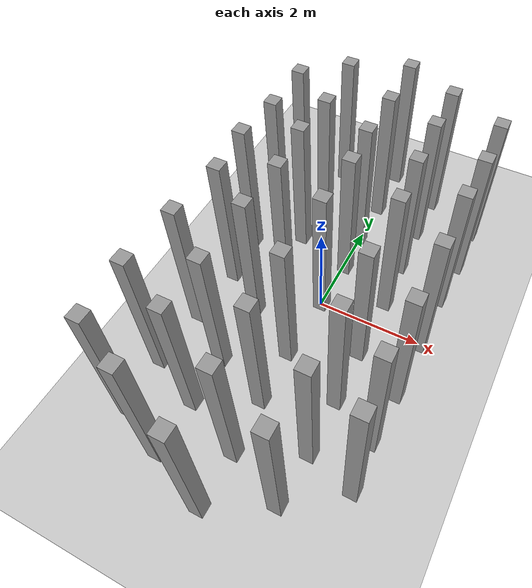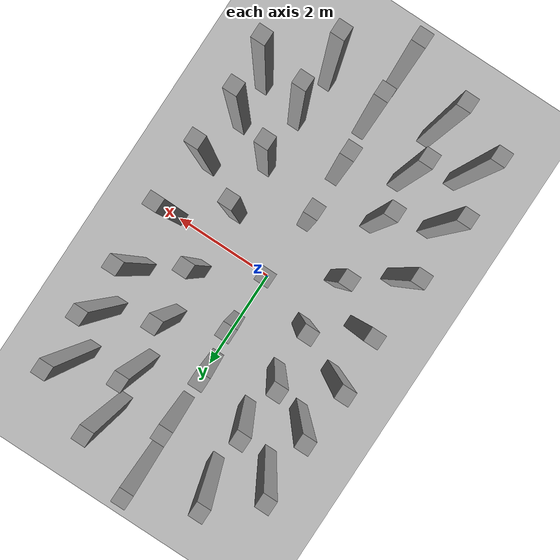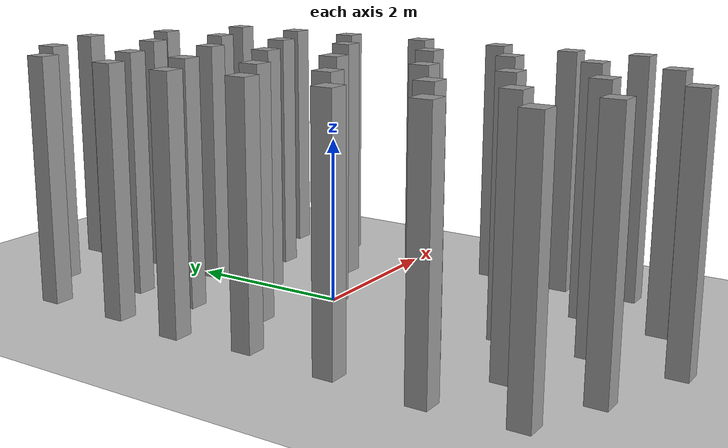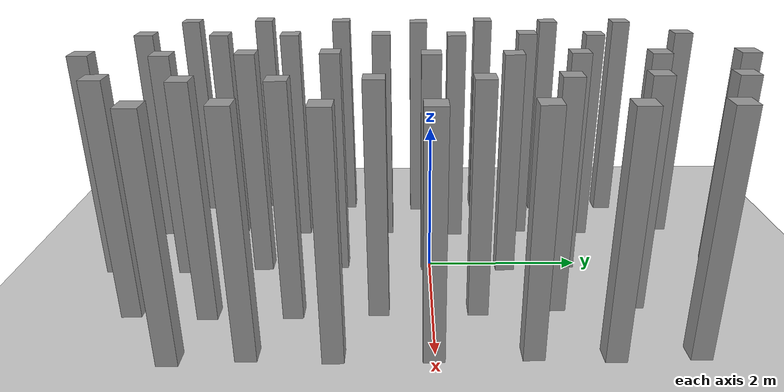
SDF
<sdf version="1.6">
 <world name="default">
  <light name="sun" type="directional">
   <pose>0 0 10 0 -0 0</pose>
   <diffuse>0.8 0.8 0.8 1</diffuse>
   <specular>0.1 0.1 0.1 1</specular>
   <attenuation>
    <range>1000</range>
    <constant>0.9</constant>
    <linear>0.01</linear>
    <quadratic>0.001</quadratic>
   </attenuation>
   <direction>-0.5 0.5 -1</direction>
  </light>
  <model name="ground_plane">
   <static>1</static>
   <link name="link">
    <collision name="collision">
     <geometry><plane><normal>0 0 1</normal><size>100 100</size></plane></geometry>
     <surface><friction><ode><mu>100</mu><mu2>50</mu2></ode></friction></surface>
    </collision>
    <visual name="visual">
     <cast_shadows>0</cast_shadows>
     <geometry><plane><normal>0 0 1</normal><size>100 100</size></plane></geometry>
     <material>
      <script><uri>file://media/materials/scripts/gazebo.material</uri><name>Gazebo/Grey</name></script>
     </material>
    </visual>
   </link>
  </model>
  <gravity>0 0 -9.8</gravity>
  <magnetic_field>6e-06 2.3e-05 -4.2e-05</magnetic_field>
  <atmosphere type="adiabatic"/>
  <physics name="default_physics" default="0" type="ode">
   <max_step_size>0.001</max_step_size>
   <real_time_factor>1</real_time_factor>
   <real_time_update_rate>1000</real_time_update_rate>
  </physics>
  <scene><ambient>0.4 0.4 0.4 1</ambient><background>0.7 0.7 0.7 1</background><shadows>1</shadows></scene>
  <spherical_coordinates>
   <surface_model>EARTH_WGS84</surface_model>
   <latitude_deg>0</latitude_deg>
   <longitude_deg>0</longitude_deg>
   <elevation>0</elevation>
   <heading_deg>0</heading_deg>
  </spherical_coordinates>
  <model name="box_2">
   <link name="link">
    <pose>0 0 1 0 -0 0</pose>
    <inertial>
     <mass>1</mass>
     <inertia><ixx>5.16667</ixx><ixy>0</ixy><ixz>0</ixz><iyy>5.16667</iyy><iyz>0</iyz><izz>5.16667</izz></inertia>
     <pose>0 0 1 0 -0 0</pose>
    </inertial>
    <visual name="ModelPreview_4::link::visual_1">
     <geometry><box><size>0.25 0.25 3</size></box></geometry>
     <material>
      <script><name>Gazebo/Grey</name><uri>file://media/materials/scripts/gazebo.material</uri></script>
      <ambient>0.3 0.3 0.3 1</ambient>
      <diffuse>0.7 0.7 0.7 1</diffuse>
      <specular>0.01 0.01 0.01 1</specular>
      <emissive>0 0 0 1</emissive>
      <shader type="vertex"><normal_map>__default__</normal_map></shader>
     </material>
    </visual>
    <visual name="visual">
     <geometry><box><size>0.25 0.25 3</size></box></geometry>
     <material>
      <script><name>Gazebo/Grey</name><uri>file://media/materials/scripts/gazebo.material</uri></script>
      <ambient>0.3 0.3 0.3 1</ambient>
      <diffuse>0.7 0.7 0.7 1</diffuse>
      <specular>0.01 0.01 0.01 1</specular>
      <emissive>0 0 0 1</emissive>
      <shader type="vertex"><normal_map>__default__</normal_map></shader>
     </material>
    </visual>
    <collision name="collision">
     <geometry><box><size>0.25 0.25 3</size></box></geometry>
     <surface>
      <friction>
       <ode><mu>1</mu><mu2>1</mu2><fdir1>0 0 0</fdir1><slip1>0</slip1><slip2>0</slip2></ode>
       <torsional>
        <coefficient>1</coefficient>
        <patch_radius>0</patch_radius>
        <surface_radius>0</surface_radius>
        <use_patch_radius>1</use_patch_radius>
        <ode><slip>0</slip></ode>
       </torsional>
      </friction>
      <bounce><restitution_coefficient>0</restitution_coefficient><threshold>1e+06</threshold></bounce>
      <contact>
       <collide_without_contact>0</collide_without_contact>
       <collide_without_contact_bitmask>1</collide_without_contact_bitmask>
       <collide_bitmask>1</collide_bitmask>
       <ode>
        <soft_cfm>0</soft_cfm>
        <soft_erp>0.2</soft_erp>
        <kp>1e+13</kp>
        <kd>1</kd>
        <max_vel>0.01</max_vel>
        <min_depth>0</min_depth>
       </ode>
       <bullet>
        <split_impulse>1</split_impulse>
        <split_impulse_penetration_threshold>-0.01</split_impulse_penetration_threshold>
        <soft_cfm>0</soft_cfm>
        <soft_erp>0.2</soft_erp>
        <kp>1e+13</kp>
        <kd>1</kd>
       </bullet>
      </contact>
     </surface>
    </collision>
   </link>
   <static>0</static>
   <pose>0.016632 0.002544 0.500001 2e-06 -6e-06 -0.000172</pose>
  </model>
  <model name="box_2_1">
   <link name="link">
    <pose>0 0 1 0 -0 0</pose>
    <inertial>
     <mass>1</mass>
     <inertia><ixx>5.16667</ixx><ixy>0</ixy><ixz>0</ixz><iyy>5.16667</iyy><iyz>0</iyz><izz>5.16667</izz></inertia>
     <pose>0 0 1 0 -0 0</pose>
    </inertial>
    <visual name="ModelPreview_4::link::visual_1">
     <geometry><box><size>0.25 0.25 3</size></box></geometry>
     <material>
      <script><name>Gazebo/Grey</name><uri>file://media/materials/scripts/gazebo.material</uri></script>
      <ambient>0.3 0.3 0.3 1</ambient>
      <diffuse>0.7 0.7 0.7 1</diffuse>
      <specular>0.01 0.01 0.01 1</specular>
      <emissive>0 0 0 1</emissive>
      <shader type="vertex"><normal_map>__default__</normal_map></shader>
     </material>
    </visual>
    <visual name="visual">
     <geometry><box><size>0.25 0.25 3</size></box></geometry>
     <material>
      <script><name>Gazebo/Grey</name><uri>file://media/materials/scripts/gazebo.material</uri></script>
      <ambient>0.3 0.3 0.3 1</ambient>
      <diffuse>0.7 0.7 0.7 1</diffuse>
      <specular>0.01 0.01 0.01 1</specular>
      <emissive>0 0 0 1</emissive>
      <shader type="vertex"><normal_map>__default__</normal_map></shader>
     </material>
    </visual>
    <collision name="collision">
     <geometry><box><size>0.25 0.25 3</size></box></geometry>
     <surface>
      <friction>
       <ode><mu>1</mu><mu2>1</mu2><fdir1>0 0 0</fdir1><slip1>0</slip1><slip2>0</slip2></ode>
       <torsional>
        <coefficient>1</coefficient>
        <patch_radius>0</patch_radius>
        <surface_radius>0</surface_radius>
        <use_patch_radius>1</use_patch_radius>
        <ode><slip>0</slip></ode>
       </torsional>
      </friction>
      <bounce><restitution_coefficient>0</restitution_coefficient><threshold>1e+06</threshold></bounce>
      <contact>
       <collide_without_contact>0</collide_without_contact>
       <collide_without_contact_bitmask>1</collide_without_contact_bitmask>
       <collide_bitmask>1</collide_bitmask>
       <ode>
        <soft_cfm>0</soft_cfm>
        <soft_erp>0.2</soft_erp>
        <kp>1e+13</kp>
        <kd>1</kd>
        <max_vel>0.01</max_vel>
        <min_depth>0</min_depth>
       </ode>
       <bullet>
        <split_impulse>1</split_impulse>
        <split_impulse_penetration_threshold>-0.01</split_impulse_penetration_threshold>
        <soft_cfm>0</soft_cfm>
        <soft_erp>0.2</soft_erp>
        <kp>1e+13</kp>
        <kd>1</kd>
       </bullet>
      </contact>
     </surface>
    </collision>
   </link>
   <static>0</static>
   <pose>-0.019064 -2.27137 0.500001 -4e-06 -2e-06 -0.000161</pose>
  </model>
  <model name="box_2_2">
   <link name="link">
    <pose>0 0 1 0 -0 0</pose>
    <inertial>
     <mass>1</mass>
     <inertia><ixx>5.16667</ixx><ixy>0</ixy><ixz>0</ixz><iyy>5.16667</iyy><iyz>0</iyz><izz>5.16667</izz></inertia>
     <pose>0 0 1 0 -0 0</pose>
    </inertial>
    <visual name="ModelPreview_4::link::visual_1">
     <geometry><box><size>0.25 0.25 3</size></box></geometry>
     <material>
      <script><name>Gazebo/Grey</name><uri>file://media/materials/scripts/gazebo.material</uri></script>
      <ambient>0.3 0.3 0.3 1</ambient>
      <diffuse>0.7 0.7 0.7 1</diffuse>
      <specular>0.01 0.01 0.01 1</specular>
      <emissive>0 0 0 1</emissive>
      <shader type="vertex"><normal_map>__default__</normal_map></shader>
     </material>
    </visual>
    <visual name="visual">
     <geometry><box><size>0.25 0.25 3</size></box></geometry>
     <material>
      <script><name>Gazebo/Grey</name><uri>file://media/materials/scripts/gazebo.material</uri></script>
      <ambient>0.3 0.3 0.3 1</ambient>
      <diffuse>0.7 0.7 0.7 1</diffuse>
      <specular>0.01 0.01 0.01 1</specular>
      <emissive>0 0 0 1</emissive>
      <shader type="vertex"><normal_map>__default__</normal_map></shader>
     </material>
    </visual>
    <collision name="collision">
     <geometry><box><size>0.25 0.25 3</size></box></geometry>
     <surface>
      <friction>
       <ode><mu>1</mu><mu2>1</mu2><fdir1>0 0 0</fdir1><slip1>0</slip1><slip2>0</slip2></ode>
       <torsional>
        <coefficient>1</coefficient>
        <patch_radius>0</patch_radius>
        <surface_radius>0</surface_radius>
        <use_patch_radius>1</use_patch_radius>
        <ode><slip>0</slip></ode>
       </torsional>
      </friction>
      <bounce><restitution_coefficient>0</restitution_coefficient><threshold>1e+06</threshold></bounce>
      <contact>
       <collide_without_contact>0</collide_without_contact>
       <collide_without_contact_bitmask>1</collide_without_contact_bitmask>
       <collide_bitmask>1</collide_bitmask>
       <ode>
        <soft_cfm>0</soft_cfm>
        <soft_erp>0.2</soft_erp>
        <kp>1e+13</kp>
        <kd>1</kd>
        <max_vel>0.01</max_vel>
        <min_depth>0</min_depth>
       </ode>
       <bullet>
        <split_impulse>1</split_impulse>
        <split_impulse_penetration_threshold>-0.01</split_impulse_penetration_threshold>
        <soft_cfm>0</soft_cfm>
        <soft_erp>0.2</soft_erp>
        <kp>1e+13</kp>
        <kd>1</kd>
       </bullet>
      </contact>
     </surface>
    </collision>
   </link>
   <static>0</static>
   <pose>0.041525 -3.28341 0.5 0 -1e-06 -0.000116</pose>
  </model>
  <model name="box_2_3">
   <link name="link">
    <pose>0 0 1 0 -0 0</pose>
    <inertial>
     <mass>1</mass>
     <inertia><ixx>5.16667</ixx><ixy>0</ixy><ixz>0</ixz><iyy>5.16667</iyy><iyz>0</iyz><izz>5.16667</izz></inertia>
     <pose>0 0 1 0 -0 0</pose>
    </inertial>
    <visual name="ModelPreview_4::link::visual_1">
     <geometry><box><size>0.25 0.25 3</size></box></geometry>
     <material>
      <script><name>Gazebo/Grey</name><uri>file://media/materials/scripts/gazebo.material</uri></script>
      <ambient>0.3 0.3 0.3 1</ambient>
      <diffuse>0.7 0.7 0.7 1</diffuse>
      <specular>0.01 0.01 0.01 1</specular>
      <emissive>0 0 0 1</emissive>
      <shader type="vertex"><normal_map>__default__</normal_map></shader>
     </material>
    </visual>
    <visual name="visual">
     <geometry><box><size>0.25 0.25 3</size></box></geometry>
     <material>
      <script><name>Gazebo/Grey</name><uri>file://media/materials/scripts/gazebo.material</uri></script>
      <ambient>0.3 0.3 0.3 1</ambient>
      <diffuse>0.7 0.7 0.7 1</diffuse>
      <specular>0.01 0.01 0.01 1</specular>
      <emissive>0 0 0 1</emissive>
      <shader type="vertex"><normal_map>__default__</normal_map></shader>
     </material>
    </visual>
    <collision name="collision">
     <geometry><box><size>0.25 0.25 3</size></box></geometry>
     <surface>
      <friction>
       <ode><mu>1</mu><mu2>1</mu2><fdir1>0 0 0</fdir1><slip1>0</slip1><slip2>0</slip2></ode>
       <torsional>
        <coefficient>1</coefficient>
        <patch_radius>0</patch_radius>
        <surface_radius>0</surface_radius>
        <use_patch_radius>1</use_patch_radius>
        <ode><slip>0</slip></ode>
       </torsional>
      </friction>
      <bounce><restitution_coefficient>0</restitution_coefficient><threshold>1e+06</threshold></bounce>
      <contact>
       <collide_without_contact>0</collide_without_contact>
       <collide_without_contact_bitmask>1</collide_without_contact_bitmask>
       <collide_bitmask>1</collide_bitmask>
       <ode>
        <soft_cfm>0</soft_cfm>
        <soft_erp>0.2</soft_erp>
        <kp>1e+13</kp>
        <kd>1</kd>
        <max_vel>0.01</max_vel>
        <min_depth>0</min_depth>
       </ode>
       <bullet>
        <split_impulse>1</split_impulse>
        <split_impulse_penetration_threshold>-0.01</split_impulse_penetration_threshold>
        <soft_cfm>0</soft_cfm>
        <soft_erp>0.2</soft_erp>
        <kp>1e+13</kp>
        <kd>1</kd>
       </bullet>
      </contact>
     </surface>
    </collision>
   </link>
   <static>0</static>
   <pose>0.019903 -4.26621 0.5 -2e-06 -0 -8.3e-05</pose>
  </model>
  <model name="box_2_7">
   <link name="link">
    <pose>0 0 1 0 -0 0</pose>
    <inertial>
     <mass>1</mass>
     <inertia><ixx>5.16667</ixx><ixy>0</ixy><ixz>0</ixz><iyy>5.16667</iyy><iyz>0</iyz><izz>5.16667</izz></inertia>
     <pose>0 0 1 0 -0 0</pose>
    </inertial>
    <visual name="ModelPreview_4::link::visual_1">
     <geometry><box><size>0.25 0.25 3</size></box></geometry>
     <material>
      <script><name>Gazebo/Grey</name><uri>file://media/materials/scripts/gazebo.material</uri></script>
      <ambient>0.3 0.3 0.3 1</ambient>
      <diffuse>0.7 0.7 0.7 1</diffuse>
      <specular>0.01 0.01 0.01 1</specular>
      <emissive>0 0 0 1</emissive>
      <shader type="vertex"><normal_map>__default__</normal_map></shader>
     </material>
    </visual>
    <visual name="visual">
     <geometry><box><size>0.25 0.25 3</size></box></geometry>
     <material>
      <script><name>Gazebo/Grey</name><uri>file://media/materials/scripts/gazebo.material</uri></script>
      <ambient>0.3 0.3 0.3 1</ambient>
      <diffuse>0.7 0.7 0.7 1</diffuse>
      <specular>0.01 0.01 0.01 1</specular>
      <emissive>0 0 0 1</emissive>
      <shader type="vertex"><normal_map>__default__</normal_map></shader>
     </material>
    </visual>
    <collision name="collision">
     <geometry><box><size>0.25 0.25 3</size></box></geometry>
     <surface>
      <friction>
       <ode><mu>1</mu><mu2>1</mu2><fdir1>0 0 0</fdir1><slip1>0</slip1><slip2>0</slip2></ode>
       <torsional>
        <coefficient>1</coefficient>
        <patch_radius>0</patch_radius>
        <surface_radius>0</surface_radius>
        <use_patch_radius>1</use_patch_radius>
        <ode><slip>0</slip></ode>
       </torsional>
      </friction>
      <bounce><restitution_coefficient>0</restitution_coefficient><threshold>1e+06</threshold></bounce>
      <contact>
       <collide_without_contact>0</collide_without_contact>
       <collide_without_contact_bitmask>1</collide_without_contact_bitmask>
       <collide_bitmask>1</collide_bitmask>
       <ode>
        <soft_cfm>0</soft_cfm>
        <soft_erp>0.2</soft_erp>
        <kp>1e+13</kp>
        <kd>1</kd>
        <max_vel>0.01</max_vel>
        <min_depth>0</min_depth>
       </ode>
       <bullet>
        <split_impulse>1</split_impulse>
        <split_impulse_penetration_threshold>-0.01</split_impulse_penetration_threshold>
        <soft_cfm>0</soft_cfm>
        <soft_erp>0.2</soft_erp>
        <kp>1e+13</kp>
        <kd>1</kd>
       </bullet>
      </contact>
     </surface>
    </collision>
   </link>
   <static>0</static>
   <pose>0.048347 1.01829 0.5 -1e-06 -0 -0.000146</pose>
  </model>
  <model name="box_2_8">
   <link name="link">
    <pose>0 0 1 0 -0 0</pose>
    <inertial>
     <mass>1</mass>
     <inertia><ixx>5.16667</ixx><ixy>0</ixy><ixz>0</ixz><iyy>5.16667</iyy><iyz>0</iyz><izz>5.16667</izz></inertia>
     <pose>0 0 1 0 -0 0</pose>
    </inertial>
    <visual name="ModelPreview_4::link::visual_1">
     <geometry><box><size>0.25 0.25 3</size></box></geometry>
     <material>
      <script><name>Gazebo/Grey</name><uri>file://media/materials/scripts/gazebo.material</uri></script>
      <ambient>0.3 0.3 0.3 1</ambient>
      <diffuse>0.7 0.7 0.7 1</diffuse>
      <specular>0.01 0.01 0.01 1</specular>
      <emissive>0 0 0 1</emissive>
      <shader type="vertex"><normal_map>__default__</normal_map></shader>
     </material>
    </visual>
    <visual name="visual">
     <geometry><box><size>0.25 0.25 3</size></box></geometry>
     <material>
      <script><name>Gazebo/Grey</name><uri>file://media/materials/scripts/gazebo.material</uri></script>
      <ambient>0.3 0.3 0.3 1</ambient>
      <diffuse>0.7 0.7 0.7 1</diffuse>
      <specular>0.01 0.01 0.01 1</specular>
      <emissive>0 0 0 1</emissive>
      <shader type="vertex"><normal_map>__default__</normal_map></shader>
     </material>
    </visual>
    <collision name="collision">
     <geometry><box><size>0.25 0.25 3</size></box></geometry>
     <surface>
      <friction>
       <ode><mu>1</mu><mu2>1</mu2><fdir1>0 0 0</fdir1><slip1>0</slip1><slip2>0</slip2></ode>
       <torsional>
        <coefficient>1</coefficient>
        <patch_radius>0</patch_radius>
        <surface_radius>0</surface_radius>
        <use_patch_radius>1</use_patch_radius>
        <ode><slip>0</slip></ode>
       </torsional>
      </friction>
      <bounce><restitution_coefficient>0</restitution_coefficient><threshold>1e+06</threshold></bounce>
      <contact>
       <collide_without_contact>0</collide_without_contact>
       <collide_without_contact_bitmask>1</collide_without_contact_bitmask>
       <collide_bitmask>1</collide_bitmask>
       <ode>
        <soft_cfm>0</soft_cfm>
        <soft_erp>0.2</soft_erp>
        <kp>1e+13</kp>
        <kd>1</kd>
        <max_vel>0.01</max_vel>
        <min_depth>0</min_depth>
       </ode>
       <bullet>
        <split_impulse>1</split_impulse>
        <split_impulse_penetration_threshold>-0.01</split_impulse_penetration_threshold>
        <soft_cfm>0</soft_cfm>
        <soft_erp>0.2</soft_erp>
        <kp>1e+13</kp>
        <kd>1</kd>
       </bullet>
      </contact>
     </surface>
    </collision>
   </link>
   <static>0</static>
   <pose>-0.013398 1.84367 0.500001 4e-06 1e-06 -0.00019</pose>
  </model>
  <model name="box_2_9">
   <link name="link">
    <pose>0 0 1 0 -0 0</pose>
    <inertial>
     <mass>1</mass>
     <inertia><ixx>5.16667</ixx><ixy>0</ixy><ixz>0</ixz><iyy>5.16667</iyy><iyz>0</iyz><izz>5.16667</izz></inertia>
     <pose>0 0 1 0 -0 0</pose>
    </inertial>
    <visual name="ModelPreview_4::link::visual_1">
     <geometry><box><size>0.25 0.25 3</size></box></geometry>
     <material>
      <script><name>Gazebo/Grey</name><uri>file://media/materials/scripts/gazebo.material</uri></script>
      <ambient>0.3 0.3 0.3 1</ambient>
      <diffuse>0.7 0.7 0.7 1</diffuse>
      <specular>0.01 0.01 0.01 1</specular>
      <emissive>0 0 0 1</emissive>
      <shader type="vertex"><normal_map>__default__</normal_map></shader>
     </material>
    </visual>
    <visual name="visual">
     <geometry><box><size>0.25 0.25 3</size></box></geometry>
     <material>
      <script><name>Gazebo/Grey</name><uri>file://media/materials/scripts/gazebo.material</uri></script>
      <ambient>0.3 0.3 0.3 1</ambient>
      <diffuse>0.7 0.7 0.7 1</diffuse>
      <specular>0.01 0.01 0.01 1</specular>
      <emissive>0 0 0 1</emissive>
      <shader type="vertex"><normal_map>__default__</normal_map></shader>
     </material>
    </visual>
    <collision name="collision">
     <geometry><box><size>0.25 0.25 3</size></box></geometry>
     <surface>
      <friction>
       <ode><mu>1</mu><mu2>1</mu2><fdir1>0 0 0</fdir1><slip1>0</slip1><slip2>0</slip2></ode>
       <torsional>
        <coefficient>1</coefficient>
        <patch_radius>0</patch_radius>
        <surface_radius>0</surface_radius>
        <use_patch_radius>1</use_patch_radius>
        <ode><slip>0</slip></ode>
       </torsional>
      </friction>
      <bounce><restitution_coefficient>0</restitution_coefficient><threshold>1e+06</threshold></bounce>
      <contact>
       <collide_without_contact>0</collide_without_contact>
       <collide_without_contact_bitmask>1</collide_without_contact_bitmask>
       <collide_bitmask>1</collide_bitmask>
       <ode>
        <soft_cfm>0</soft_cfm>
        <soft_erp>0.2</soft_erp>
        <kp>1e+13</kp>
        <kd>1</kd>
        <max_vel>0.01</max_vel>
        <min_depth>0</min_depth>
       </ode>
       <bullet>
        <split_impulse>1</split_impulse>
        <split_impulse_penetration_threshold>-0.01</split_impulse_penetration_threshold>
        <soft_cfm>0</soft_cfm>
        <soft_erp>0.2</soft_erp>
        <kp>1e+13</kp>
        <kd>1</kd>
       </bullet>
      </contact>
     </surface>
    </collision>
   </link>
   <static>0</static>
   <pose>0.00864 2.82554 0.500002 1.5e-05 -1e-06 -0.000131</pose>
  </model>
  <model name="box_2_10">
   <link name="link">
    <pose>0 0 1 0 -0 0</pose>
    <inertial>
     <mass>1</mass>
     <inertia><ixx>5.16667</ixx><ixy>0</ixy><ixz>0</ixz><iyy>5.16667</iyy><iyz>0</iyz><izz>5.16667</izz></inertia>
     <pose>0 0 1 0 -0 0</pose>
    </inertial>
    <visual name="ModelPreview_4::link::visual_1">
     <geometry><box><size>0.25 0.25 3</size></box></geometry>
     <material>
      <script><name>Gazebo/Grey</name><uri>file://media/materials/scripts/gazebo.material</uri></script>
      <ambient>0.3 0.3 0.3 1</ambient>
      <diffuse>0.7 0.7 0.7 1</diffuse>
      <specular>0.01 0.01 0.01 1</specular>
      <emissive>0 0 0 1</emissive>
      <shader type="vertex"><normal_map>__default__</normal_map></shader>
     </material>
    </visual>
    <visual name="visual">
     <geometry><box><size>0.25 0.25 3</size></box></geometry>
     <material>
      <script><name>Gazebo/Grey</name><uri>file://media/materials/scripts/gazebo.material</uri></script>
      <ambient>0.3 0.3 0.3 1</ambient>
      <diffuse>0.7 0.7 0.7 1</diffuse>
      <specular>0.01 0.01 0.01 1</specular>
      <emissive>0 0 0 1</emissive>
      <shader type="vertex"><normal_map>__default__</normal_map></shader>
     </material>
    </visual>
    <collision name="collision">
     <geometry><box><size>0.25 0.25 3</size></box></geometry>
     <surface>
      <friction>
       <ode><mu>1</mu><mu2>1</mu2><fdir1>0 0 0</fdir1><slip1>0</slip1><slip2>0</slip2></ode>
       <torsional>
        <coefficient>1</coefficient>
        <patch_radius>0</patch_radius>
        <surface_radius>0</surface_radius>
        <use_patch_radius>1</use_patch_radius>
        <ode><slip>0</slip></ode>
       </torsional>
      </friction>
      <bounce><restitution_coefficient>0</restitution_coefficient><threshold>1e+06</threshold></bounce>
      <contact>
       <collide_without_contact>0</collide_without_contact>
       <collide_without_contact_bitmask>1</collide_without_contact_bitmask>
       <collide_bitmask>1</collide_bitmask>
       <ode>
        <soft_cfm>0</soft_cfm>
        <soft_erp>0.2</soft_erp>
        <kp>1e+13</kp>
        <kd>1</kd>
        <max_vel>0.01</max_vel>
        <min_depth>0</min_depth>
       </ode>
       <bullet>
        <split_impulse>1</split_impulse>
        <split_impulse_penetration_threshold>-0.01</split_impulse_penetration_threshold>
        <soft_cfm>0</soft_cfm>
        <soft_erp>0.2</soft_erp>
        <kp>1e+13</kp>
        <kd>1</kd>
       </bullet>
      </contact>
     </surface>
    </collision>
   </link>
   <static>0</static>
   <pose>-0.018716 3.93322 0.5 0 -2e-06 -0.000108</pose>
  </model>
  <model name="box_2_11">
   <link name="link">
    <pose>0 0 1 0 -0 0</pose>
    <inertial>
     <mass>1</mass>
     <inertia><ixx>5.16667</ixx><ixy>0</ixy><ixz>0</ixz><iyy>5.16667</iyy><iyz>0</iyz><izz>5.16667</izz></inertia>
     <pose>0 0 1 0 -0 0</pose>
    </inertial>
    <visual name="ModelPreview_4::link::visual_1">
     <geometry><box><size>0.25 0.25 3</size></box></geometry>
     <material>
      <script><name>Gazebo/Grey</name><uri>file://media/materials/scripts/gazebo.material</uri></script>
      <ambient>0.3 0.3 0.3 1</ambient>
      <diffuse>0.7 0.7 0.7 1</diffuse>
      <specular>0.01 0.01 0.01 1</specular>
      <emissive>0 0 0 1</emissive>
      <shader type="vertex"><normal_map>__default__</normal_map></shader>
     </material>
    </visual>
    <visual name="visual">
     <geometry><box><size>0.25 0.25 3</size></box></geometry>
     <material>
      <script><name>Gazebo/Grey</name><uri>file://media/materials/scripts/gazebo.material</uri></script>
      <ambient>0.3 0.3 0.3 1</ambient>
      <diffuse>0.7 0.7 0.7 1</diffuse>
      <specular>0.01 0.01 0.01 1</specular>
      <emissive>0 0 0 1</emissive>
      <shader type="vertex"><normal_map>__default__</normal_map></shader>
     </material>
    </visual>
    <collision name="collision">
     <geometry><box><size>0.25 0.25 3</size></box></geometry>
     <surface>
      <friction>
       <ode><mu>1</mu><mu2>1</mu2><fdir1>0 0 0</fdir1><slip1>0</slip1><slip2>0</slip2></ode>
       <torsional>
        <coefficient>1</coefficient>
        <patch_radius>0</patch_radius>
        <surface_radius>0</surface_radius>
        <use_patch_radius>1</use_patch_radius>
        <ode><slip>0</slip></ode>
       </torsional>
      </friction>
      <bounce><restitution_coefficient>0</restitution_coefficient><threshold>1e+06</threshold></bounce>
      <contact>
       <collide_without_contact>0</collide_without_contact>
       <collide_without_contact_bitmask>1</collide_without_contact_bitmask>
       <collide_bitmask>1</collide_bitmask>
       <ode>
        <soft_cfm>0</soft_cfm>
        <soft_erp>0.2</soft_erp>
        <kp>1e+13</kp>
        <kd>1</kd>
        <max_vel>0.01</max_vel>
        <min_depth>0</min_depth>
       </ode>
       <bullet>
        <split_impulse>1</split_impulse>
        <split_impulse_penetration_threshold>-0.01</split_impulse_penetration_threshold>
        <soft_cfm>0</soft_cfm>
        <soft_erp>0.2</soft_erp>
        <kp>1e+13</kp>
        <kd>1</kd>
       </bullet>
      </contact>
     </surface>
    </collision>
   </link>
   <static>0</static>
   <pose>-0.046444 -1.24226 0.5 1e-06 -2e-06 -0.000162</pose>
  </model>
  <model name="box_2_12">
   <link name="link">
    <pose>0 0 1 0 -0 0</pose>
    <inertial>
     <mass>1</mass>
     <inertia><ixx>5.16667</ixx><ixy>0</ixy><ixz>0</ixz><iyy>5.16667</iyy><iyz>0</iyz><izz>5.16667</izz></inertia>
     <pose>0 0 1 0 -0 0</pose>
    </inertial>
    <visual name="ModelPreview_4::link::visual_1">
     <geometry><box><size>0.25 0.25 3</size></box></geometry>
     <material>
      <script><name>Gazebo/Grey</name><uri>file://media/materials/scripts/gazebo.material</uri></script>
      <ambient>0.3 0.3 0.3 1</ambient>
      <diffuse>0.7 0.7 0.7 1</diffuse>
      <specular>0.01 0.01 0.01 1</specular>
      <emissive>0 0 0 1</emissive>
      <shader type="vertex"><normal_map>__default__</normal_map></shader>
     </material>
    </visual>
    <visual name="visual">
     <geometry><box><size>0.25 0.25 3</size></box></geometry>
     <material>
      <script><name>Gazebo/Grey</name><uri>file://media/materials/scripts/gazebo.material</uri></script>
      <ambient>0.3 0.3 0.3 1</ambient>
      <diffuse>0.7 0.7 0.7 1</diffuse>
      <specular>0.01 0.01 0.01 1</specular>
      <emissive>0 0 0 1</emissive>
      <shader type="vertex"><normal_map>__default__</normal_map></shader>
     </material>
    </visual>
    <collision name="collision">
     <geometry><box><size>0.25 0.25 3</size></box></geometry>
     <surface>
      <friction>
       <ode><mu>1</mu><mu2>1</mu2><fdir1>0 0 0</fdir1><slip1>0</slip1><slip2>0</slip2></ode>
       <torsional>
        <coefficient>1</coefficient>
        <patch_radius>0</patch_radius>
        <surface_radius>0</surface_radius>
        <use_patch_radius>1</use_patch_radius>
        <ode><slip>0</slip></ode>
       </torsional>
      </friction>
      <bounce><restitution_coefficient>0</restitution_coefficient><threshold>1e+06</threshold></bounce>
      <contact>
       <collide_without_contact>0</collide_without_contact>
       <collide_without_contact_bitmask>1</collide_without_contact_bitmask>
       <collide_bitmask>1</collide_bitmask>
       <ode>
        <soft_cfm>0</soft_cfm>
        <soft_erp>0.2</soft_erp>
        <kp>1e+13</kp>
        <kd>1</kd>
        <max_vel>0.01</max_vel>
        <min_depth>0</min_depth>
       </ode>
       <bullet>
        <split_impulse>1</split_impulse>
        <split_impulse_penetration_threshold>-0.01</split_impulse_penetration_threshold>
        <soft_cfm>0</soft_cfm>
        <soft_erp>0.2</soft_erp>
        <kp>1e+13</kp>
        <kd>1</kd>
       </bullet>
      </contact>
     </surface>
    </collision>
   </link>
   <static>0</static>
   <pose>1.08723 -3.69589 0.5 0 0 -8.7e-05</pose>
  </model>
  <model name="box_2_13">
   <link name="link">
    <pose>0 0 1 0 -0 0</pose>
    <inertial>
     <mass>1</mass>
     <inertia><ixx>5.16667</ixx><ixy>0</ixy><ixz>0</ixz><iyy>5.16667</iyy><iyz>0</iyz><izz>5.16667</izz></inertia>
     <pose>0 0 1 0 -0 0</pose>
    </inertial>
    <visual name="ModelPreview_4::link::visual_1">
     <geometry><box><size>0.25 0.25 3</size></box></geometry>
     <material>
      <script><name>Gazebo/Grey</name><uri>file://media/materials/scripts/gazebo.material</uri></script>
      <ambient>0.3 0.3 0.3 1</ambient>
      <diffuse>0.7 0.7 0.7 1</diffuse>
      <specular>0.01 0.01 0.01 1</specular>
      <emissive>0 0 0 1</emissive>
      <shader type="vertex"><normal_map>__default__</normal_map></shader>
     </material>
    </visual>
    <visual name="visual">
     <geometry><box><size>0.25 0.25 3</size></box></geometry>
     <material>
      <script><name>Gazebo/Grey</name><uri>file://media/materials/scripts/gazebo.material</uri></script>
      <ambient>0.3 0.3 0.3 1</ambient>
      <diffuse>0.7 0.7 0.7 1</diffuse>
      <specular>0.01 0.01 0.01 1</specular>
      <emissive>0 0 0 1</emissive>
      <shader type="vertex"><normal_map>__default__</normal_map></shader>
     </material>
    </visual>
    <collision name="collision">
     <geometry><box><size>0.25 0.25 3</size></box></geometry>
     <surface>
      <friction>
       <ode><mu>1</mu><mu2>1</mu2><fdir1>0 0 0</fdir1><slip1>0</slip1><slip2>0</slip2></ode>
       <torsional>
        <coefficient>1</coefficient>
        <patch_radius>0</patch_radius>
        <surface_radius>0</surface_radius>
        <use_patch_radius>1</use_patch_radius>
        <ode><slip>0</slip></ode>
       </torsional>
      </friction>
      <bounce><restitution_coefficient>0</restitution_coefficient><threshold>1e+06</threshold></bounce>
      <contact>
       <collide_without_contact>0</collide_without_contact>
       <collide_without_contact_bitmask>1</collide_without_contact_bitmask>
       <collide_bitmask>1</collide_bitmask>
       <ode>
        <soft_cfm>0</soft_cfm>
        <soft_erp>0.2</soft_erp>
        <kp>1e+13</kp>
        <kd>1</kd>
        <max_vel>0.01</max_vel>
        <min_depth>0</min_depth>
       </ode>
       <bullet>
        <split_impulse>1</split_impulse>
        <split_impulse_penetration_threshold>-0.01</split_impulse_penetration_threshold>
        <soft_cfm>0</soft_cfm>
        <soft_erp>0.2</soft_erp>
        <kp>1e+13</kp>
        <kd>1</kd>
       </bullet>
      </contact>
     </surface>
    </collision>
   </link>
   <static>0</static>
   <pose>1.15505 -2.75172 0.500002 -1.5e-05 0 -0.000181</pose>
  </model>
  <model name="box_2_14">
   <link name="link">
    <pose>0 0 1 0 -0 0</pose>
    <inertial>
     <mass>1</mass>
     <inertia><ixx>5.16667</ixx><ixy>0</ixy><ixz>0</ixz><iyy>5.16667</iyy><iyz>0</iyz><izz>5.16667</izz></inertia>
     <pose>0 0 1 0 -0 0</pose>
    </inertial>
    <visual name="ModelPreview_4::link::visual_1">
     <geometry><box><size>0.25 0.25 3</size></box></geometry>
     <material>
      <script><name>Gazebo/Grey</name><uri>file://media/materials/scripts/gazebo.material</uri></script>
      <ambient>0.3 0.3 0.3 1</ambient>
      <diffuse>0.7 0.7 0.7 1</diffuse>
      <specular>0.01 0.01 0.01 1</specular>
      <emissive>0 0 0 1</emissive>
      <shader type="vertex"><normal_map>__default__</normal_map></shader>
     </material>
    </visual>
    <visual name="visual">
     <geometry><box><size>0.25 0.25 3</size></box></geometry>
     <material>
      <script><name>Gazebo/Grey</name><uri>file://media/materials/scripts/gazebo.material</uri></script>
      <ambient>0.3 0.3 0.3 1</ambient>
      <diffuse>0.7 0.7 0.7 1</diffuse>
      <specular>0.01 0.01 0.01 1</specular>
      <emissive>0 0 0 1</emissive>
      <shader type="vertex"><normal_map>__default__</normal_map></shader>
     </material>
    </visual>
    <collision name="collision">
     <geometry><box><size>0.25 0.25 3</size></box></geometry>
     <surface>
      <friction>
       <ode><mu>1</mu><mu2>1</mu2><fdir1>0 0 0</fdir1><slip1>0</slip1><slip2>0</slip2></ode>
       <torsional>
        <coefficient>1</coefficient>
        <patch_radius>0</patch_radius>
        <surface_radius>0</surface_radius>
        <use_patch_radius>1</use_patch_radius>
        <ode><slip>0</slip></ode>
       </torsional>
      </friction>
      <bounce><restitution_coefficient>0</restitution_coefficient><threshold>1e+06</threshold></bounce>
      <contact>
       <collide_without_contact>0</collide_without_contact>
       <collide_without_contact_bitmask>1</collide_without_contact_bitmask>
       <collide_bitmask>1</collide_bitmask>
       <ode>
        <soft_cfm>0</soft_cfm>
        <soft_erp>0.2</soft_erp>
        <kp>1e+13</kp>
        <kd>1</kd>
        <max_vel>0.01</max_vel>
        <min_depth>0</min_depth>
       </ode>
       <bullet>
        <split_impulse>1</split_impulse>
        <split_impulse_penetration_threshold>-0.01</split_impulse_penetration_threshold>
        <soft_cfm>0</soft_cfm>
        <soft_erp>0.2</soft_erp>
        <kp>1e+13</kp>
        <kd>1</kd>
       </bullet>
      </contact>
     </surface>
    </collision>
   </link>
   <static>0</static>
   <pose>1.14542 -1.70799 0.5 0 0 -0.00016</pose>
  </model>
  <model name="box_2_15">
   <link name="link">
    <pose>0 0 1 0 -0 0</pose>
    <inertial>
     <mass>1</mass>
     <inertia><ixx>5.16667</ixx><ixy>0</ixy><ixz>0</ixz><iyy>5.16667</iyy><iyz>0</iyz><izz>5.16667</izz></inertia>
     <pose>0 0 1 0 -0 0</pose>
    </inertial>
    <visual name="ModelPreview_4::link::visual_1">
     <geometry><box><size>0.25 0.25 3</size></box></geometry>
     <material>
      <script><name>Gazebo/Grey</name><uri>file://media/materials/scripts/gazebo.material</uri></script>
      <ambient>0.3 0.3 0.3 1</ambient>
      <diffuse>0.7 0.7 0.7 1</diffuse>
      <specular>0.01 0.01 0.01 1</specular>
      <emissive>0 0 0 1</emissive>
      <shader type="vertex"><normal_map>__default__</normal_map></shader>
     </material>
    </visual>
    <visual name="visual">
     <geometry><box><size>0.25 0.25 3</size></box></geometry>
     <material>
      <script><name>Gazebo/Grey</name><uri>file://media/materials/scripts/gazebo.material</uri></script>
      <ambient>0.3 0.3 0.3 1</ambient>
      <diffuse>0.7 0.7 0.7 1</diffuse>
      <specular>0.01 0.01 0.01 1</specular>
      <emissive>0 0 0 1</emissive>
      <shader type="vertex"><normal_map>__default__</normal_map></shader>
     </material>
    </visual>
    <collision name="collision">
     <geometry><box><size>0.25 0.25 3</size></box></geometry>
     <surface>
      <friction>
       <ode><mu>1</mu><mu2>1</mu2><fdir1>0 0 0</fdir1><slip1>0</slip1><slip2>0</slip2></ode>
       <torsional>
        <coefficient>1</coefficient>
        <patch_radius>0</patch_radius>
        <surface_radius>0</surface_radius>
        <use_patch_radius>1</use_patch_radius>
        <ode><slip>0</slip></ode>
       </torsional>
      </friction>
      <bounce><restitution_coefficient>0</restitution_coefficient><threshold>1e+06</threshold></bounce>
      <contact>
       <collide_without_contact>0</collide_without_contact>
       <collide_without_contact_bitmask>1</collide_without_contact_bitmask>
       <collide_bitmask>1</collide_bitmask>
       <ode>
        <soft_cfm>0</soft_cfm>
        <soft_erp>0.2</soft_erp>
        <kp>1e+13</kp>
        <kd>1</kd>
        <max_vel>0.01</max_vel>
        <min_depth>0</min_depth>
       </ode>
       <bullet>
        <split_impulse>1</split_impulse>
        <split_impulse_penetration_threshold>-0.01</split_impulse_penetration_threshold>
        <soft_cfm>0</soft_cfm>
        <soft_erp>0.2</soft_erp>
        <kp>1e+13</kp>
        <kd>1</kd>
       </bullet>
      </contact>
     </surface>
    </collision>
   </link>
   <static>0</static>
   <pose>1.10372 -0.662154 0.5 0 0 -0.000185</pose>
  </model>
  <model name="box_2_16">
   <link name="link">
    <pose>0 0 1 0 -0 0</pose>
    <inertial>
     <mass>1</mass>
     <inertia><ixx>5.16667</ixx><ixy>0</ixy><ixz>0</ixz><iyy>5.16667</iyy><iyz>0</iyz><izz>5.16667</izz></inertia>
     <pose>0 0 1 0 -0 0</pose>
    </inertial>
    <visual name="ModelPreview_4::link::visual_1">
     <geometry><box><size>0.25 0.25 3</size></box></geometry>
     <material>
      <script><name>Gazebo/Grey</name><uri>file://media/materials/scripts/gazebo.material</uri></script>
      <ambient>0.3 0.3 0.3 1</ambient>
      <diffuse>0.7 0.7 0.7 1</diffuse>
      <specular>0.01 0.01 0.01 1</specular>
      <emissive>0 0 0 1</emissive>
      <shader type="vertex"><normal_map>__default__</normal_map></shader>
     </material>
    </visual>
    <visual name="visual">
     <geometry><box><size>0.25 0.25 3</size></box></geometry>
     <material>
      <script><name>Gazebo/Grey</name><uri>file://media/materials/scripts/gazebo.material</uri></script>
      <ambient>0.3 0.3 0.3 1</ambient>
      <diffuse>0.7 0.7 0.7 1</diffuse>
      <specular>0.01 0.01 0.01 1</specular>
      <emissive>0 0 0 1</emissive>
      <shader type="vertex"><normal_map>__default__</normal_map></shader>
     </material>
    </visual>
    <collision name="collision">
     <geometry><box><size>0.25 0.25 3</size></box></geometry>
     <surface>
      <friction>
       <ode><mu>1</mu><mu2>1</mu2><fdir1>0 0 0</fdir1><slip1>0</slip1><slip2>0</slip2></ode>
       <torsional>
        <coefficient>1</coefficient>
        <patch_radius>0</patch_radius>
        <surface_radius>0</surface_radius>
        <use_patch_radius>1</use_patch_radius>
        <ode><slip>0</slip></ode>
       </torsional>
      </friction>
      <bounce><restitution_coefficient>0</restitution_coefficient><threshold>1e+06</threshold></bounce>
      <contact>
       <collide_without_contact>0</collide_without_contact>
       <collide_without_contact_bitmask>1</collide_without_contact_bitmask>
       <collide_bitmask>1</collide_bitmask>
       <ode>
        <soft_cfm>0</soft_cfm>
        <soft_erp>0.2</soft_erp>
        <kp>1e+13</kp>
        <kd>1</kd>
        <max_vel>0.01</max_vel>
        <min_depth>0</min_depth>
       </ode>
       <bullet>
        <split_impulse>1</split_impulse>
        <split_impulse_penetration_threshold>-0.01</split_impulse_penetration_threshold>
        <soft_cfm>0</soft_cfm>
        <soft_erp>0.2</soft_erp>
        <kp>1e+13</kp>
        <kd>1</kd>
       </bullet>
      </contact>
     </surface>
    </collision>
   </link>
   <static>0</static>
   <pose>1.11047 0.557185 0.5 0 2e-06 -9.3e-05</pose>
  </model>
  <model name="box_2_17">
   <link name="link">
    <pose>0 0 1 0 -0 0</pose>
    <inertial>
     <mass>1</mass>
     <inertia><ixx>5.16667</ixx><ixy>0</ixy><ixz>0</ixz><iyy>5.16667</iyy><iyz>0</iyz><izz>5.16667</izz></inertia>
     <pose>0 0 1 0 -0 0</pose>
    </inertial>
    <visual name="ModelPreview_4::link::visual_1">
     <geometry><box><size>0.25 0.25 3</size></box></geometry>
     <material>
      <script><name>Gazebo/Grey</name><uri>file://media/materials/scripts/gazebo.material</uri></script>
      <ambient>0.3 0.3 0.3 1</ambient>
      <diffuse>0.7 0.7 0.7 1</diffuse>
      <specular>0.01 0.01 0.01 1</specular>
      <emissive>0 0 0 1</emissive>
      <shader type="vertex"><normal_map>__default__</normal_map></shader>
     </material>
    </visual>
    <visual name="visual">
     <geometry><box><size>0.25 0.25 3</size></box></geometry>
     <material>
      <script><name>Gazebo/Grey</name><uri>file://media/materials/scripts/gazebo.material</uri></script>
      <ambient>0.3 0.3 0.3 1</ambient>
      <diffuse>0.7 0.7 0.7 1</diffuse>
      <specular>0.01 0.01 0.01 1</specular>
      <emissive>0 0 0 1</emissive>
      <shader type="vertex"><normal_map>__default__</normal_map></shader>
     </material>
    </visual>
    <collision name="collision">
     <geometry><box><size>0.25 0.25 3</size></box></geometry>
     <surface>
      <friction>
       <ode><mu>1</mu><mu2>1</mu2><fdir1>0 0 0</fdir1><slip1>0</slip1><slip2>0</slip2></ode>
       <torsional>
        <coefficient>1</coefficient>
        <patch_radius>0</patch_radius>
        <surface_radius>0</surface_radius>
        <use_patch_radius>1</use_patch_radius>
        <ode><slip>0</slip></ode>
       </torsional>
      </friction>
      <bounce><restitution_coefficient>0</restitution_coefficient><threshold>1e+06</threshold></bounce>
      <contact>
       <collide_without_contact>0</collide_without_contact>
       <collide_without_contact_bitmask>1</collide_without_contact_bitmask>
       <collide_bitmask>1</collide_bitmask>
       <ode>
        <soft_cfm>0</soft_cfm>
        <soft_erp>0.2</soft_erp>
        <kp>1e+13</kp>
        <kd>1</kd>
        <max_vel>0.01</max_vel>
        <min_depth>0</min_depth>
       </ode>
       <bullet>
        <split_impulse>1</split_impulse>
        <split_impulse_penetration_threshold>-0.01</split_impulse_penetration_threshold>
        <soft_cfm>0</soft_cfm>
        <soft_erp>0.2</soft_erp>
        <kp>1e+13</kp>
        <kd>1</kd>
       </bullet>
      </contact>
     </surface>
    </collision>
   </link>
   <static>0</static>
   <pose>1.03676 1.52247 0.500001 -9e-06 3e-06 -0.000119</pose>
  </model>
  <model name="box_2_18">
   <link name="link">
    <pose>0 0 1 0 -0 0</pose>
    <inertial>
     <mass>1</mass>
     <inertia><ixx>5.16667</ixx><ixy>0</ixy><ixz>0</ixz><iyy>5.16667</iyy><iyz>0</iyz><izz>5.16667</izz></inertia>
     <pose>0 0 1 0 -0 0</pose>
    </inertial>
    <visual name="ModelPreview_4::link::visual_1">
     <geometry><box><size>0.25 0.25 3</size></box></geometry>
     <material>
      <script><name>Gazebo/Grey</name><uri>file://media/materials/scripts/gazebo.material</uri></script>
      <ambient>0.3 0.3 0.3 1</ambient>
      <diffuse>0.7 0.7 0.7 1</diffuse>
      <specular>0.01 0.01 0.01 1</specular>
      <emissive>0 0 0 1</emissive>
      <shader type="vertex"><normal_map>__default__</normal_map></shader>
     </material>
    </visual>
    <visual name="visual">
     <geometry><box><size>0.25 0.25 3</size></box></geometry>
     <material>
      <script><name>Gazebo/Grey</name><uri>file://media/materials/scripts/gazebo.material</uri></script>
      <ambient>0.3 0.3 0.3 1</ambient>
      <diffuse>0.7 0.7 0.7 1</diffuse>
      <specular>0.01 0.01 0.01 1</specular>
      <emissive>0 0 0 1</emissive>
      <shader type="vertex"><normal_map>__default__</normal_map></shader>
     </material>
    </visual>
    <collision name="collision">
     <geometry><box><size>0.25 0.25 3</size></box></geometry>
     <surface>
      <friction>
       <ode><mu>1</mu><mu2>1</mu2><fdir1>0 0 0</fdir1><slip1>0</slip1><slip2>0</slip2></ode>
       <torsional>
        <coefficient>1</coefficient>
        <patch_radius>0</patch_radius>
        <surface_radius>0</surface_radius>
        <use_patch_radius>1</use_patch_radius>
        <ode><slip>0</slip></ode>
       </torsional>
      </friction>
      <bounce><restitution_coefficient>0</restitution_coefficient><threshold>1e+06</threshold></bounce>
      <contact>
       <collide_without_contact>0</collide_without_contact>
       <collide_without_contact_bitmask>1</collide_without_contact_bitmask>
       <collide_bitmask>1</collide_bitmask>
       <ode>
        <soft_cfm>0</soft_cfm>
        <soft_erp>0.2</soft_erp>
        <kp>1e+13</kp>
        <kd>1</kd>
        <max_vel>0.01</max_vel>
        <min_depth>0</min_depth>
       </ode>
       <bullet>
        <split_impulse>1</split_impulse>
        <split_impulse_penetration_threshold>-0.01</split_impulse_penetration_threshold>
        <soft_cfm>0</soft_cfm>
        <soft_erp>0.2</soft_erp>
        <kp>1e+13</kp>
        <kd>1</kd>
       </bullet>
      </contact>
     </surface>
    </collision>
   </link>
   <static>0</static>
   <pose>0.994585 2.51688 0.500001 -8e-06 1e-06 -0.000181</pose>
  </model>
  <model name="box_2_19">
   <link name="link">
    <pose>0 0 1 0 -0 0</pose>
    <inertial>
     <mass>1</mass>
     <inertia><ixx>5.16667</ixx><ixy>0</ixy><ixz>0</ixz><iyy>5.16667</iyy><iyz>0</iyz><izz>5.16667</izz></inertia>
     <pose>0 0 1 0 -0 0</pose>
    </inertial>
    <visual name="ModelPreview_4::link::visual_1">
     <geometry><box><size>0.25 0.25 3</size></box></geometry>
     <material>
      <script><name>Gazebo/Grey</name><uri>file://media/materials/scripts/gazebo.material</uri></script>
      <ambient>0.3 0.3 0.3 1</ambient>
      <diffuse>0.7 0.7 0.7 1</diffuse>
      <specular>0.01 0.01 0.01 1</specular>
      <emissive>0 0 0 1</emissive>
      <shader type="vertex"><normal_map>__default__</normal_map></shader>
     </material>
    </visual>
    <visual name="visual">
     <geometry><box><size>0.25 0.25 3</size></box></geometry>
     <material>
      <script><name>Gazebo/Grey</name><uri>file://media/materials/scripts/gazebo.material</uri></script>
      <ambient>0.3 0.3 0.3 1</ambient>
      <diffuse>0.7 0.7 0.7 1</diffuse>
      <specular>0.01 0.01 0.01 1</specular>
      <emissive>0 0 0 1</emissive>
      <shader type="vertex"><normal_map>__default__</normal_map></shader>
     </material>
    </visual>
    <collision name="collision">
     <geometry><box><size>0.25 0.25 3</size></box></geometry>
     <surface>
      <friction>
       <ode><mu>1</mu><mu2>1</mu2><fdir1>0 0 0</fdir1><slip1>0</slip1><slip2>0</slip2></ode>
       <torsional>
        <coefficient>1</coefficient>
        <patch_radius>0</patch_radius>
        <surface_radius>0</surface_radius>
        <use_patch_radius>1</use_patch_radius>
        <ode><slip>0</slip></ode>
       </torsional>
      </friction>
      <bounce><restitution_coefficient>0</restitution_coefficient><threshold>1e+06</threshold></bounce>
      <contact>
       <collide_without_contact>0</collide_without_contact>
       <collide_without_contact_bitmask>1</collide_without_contact_bitmask>
       <collide_bitmask>1</collide_bitmask>
       <ode>
        <soft_cfm>0</soft_cfm>
        <soft_erp>0.2</soft_erp>
        <kp>1e+13</kp>
        <kd>1</kd>
        <max_vel>0.01</max_vel>
        <min_depth>0</min_depth>
       </ode>
       <bullet>
        <split_impulse>1</split_impulse>
        <split_impulse_penetration_threshold>-0.01</split_impulse_penetration_threshold>
        <soft_cfm>0</soft_cfm>
        <soft_erp>0.2</soft_erp>
        <kp>1e+13</kp>
        <kd>1</kd>
       </bullet>
      </contact>
     </surface>
    </collision>
   </link>
   <static>0</static>
   <pose>0.987452 3.4768 0.500001 9e-06 0 -0.000152</pose>
  </model>
  <model name="box_2_20">
   <link name="link">
    <pose>0 0 1 0 -0 0</pose>
    <inertial>
     <mass>1</mass>
     <inertia><ixx>5.16667</ixx><ixy>0</ixy><ixz>0</ixz><iyy>5.16667</iyy><iyz>0</iyz><izz>5.16667</izz></inertia>
     <pose>0 0 1 0 -0 0</pose>
    </inertial>
    <visual name="ModelPreview_4::link::visual_1">
     <geometry><box><size>0.25 0.25 3</size></box></geometry>
     <material>
      <script><name>Gazebo/Grey</name><uri>file://media/materials/scripts/gazebo.material</uri></script>
      <ambient>0.3 0.3 0.3 1</ambient>
      <diffuse>0.7 0.7 0.7 1</diffuse>
      <specular>0.01 0.01 0.01 1</specular>
      <emissive>0 0 0 1</emissive>
      <shader type="vertex"><normal_map>__default__</normal_map></shader>
     </material>
    </visual>
    <visual name="visual">
     <geometry><box><size>0.25 0.25 3</size></box></geometry>
     <material>
      <script><name>Gazebo/Grey</name><uri>file://media/materials/scripts/gazebo.material</uri></script>
      <ambient>0.3 0.3 0.3 1</ambient>
      <diffuse>0.7 0.7 0.7 1</diffuse>
      <specular>0.01 0.01 0.01 1</specular>
      <emissive>0 0 0 1</emissive>
      <shader type="vertex"><normal_map>__default__</normal_map></shader>
     </material>
    </visual>
    <collision name="collision">
     <geometry><box><size>0.25 0.25 3</size></box></geometry>
     <surface>
      <friction>
       <ode><mu>1</mu><mu2>1</mu2><fdir1>0 0 0</fdir1><slip1>0</slip1><slip2>0</slip2></ode>
       <torsional>
        <coefficient>1</coefficient>
        <patch_radius>0</patch_radius>
        <surface_radius>0</surface_radius>
        <use_patch_radius>1</use_patch_radius>
        <ode><slip>0</slip></ode>
       </torsional>
      </friction>
      <bounce><restitution_coefficient>0</restitution_coefficient><threshold>1e+06</threshold></bounce>
      <contact>
       <collide_without_contact>0</collide_without_contact>
       <collide_without_contact_bitmask>1</collide_without_contact_bitmask>
       <collide_bitmask>1</collide_bitmask>
       <ode>
        <soft_cfm>0</soft_cfm>
        <soft_erp>0.2</soft_erp>
        <kp>1e+13</kp>
        <kd>1</kd>
        <max_vel>0.01</max_vel>
        <min_depth>0</min_depth>
       </ode>
       <bullet>
        <split_impulse>1</split_impulse>
        <split_impulse_penetration_threshold>-0.01</split_impulse_penetration_threshold>
        <soft_cfm>0</soft_cfm>
        <soft_erp>0.2</soft_erp>
        <kp>1e+13</kp>
        <kd>1</kd>
       </bullet>
      </contact>
     </surface>
    </collision>
   </link>
   <static>0</static>
   <pose>-1.09874 3.47591 0.5 -3e-06 -0 -0.00021</pose>
  </model>
  <model name="box_2_21">
   <link name="link">
    <pose>0 0 1 0 -0 0</pose>
    <inertial>
     <mass>1</mass>
     <inertia><ixx>5.16667</ixx><ixy>0</ixy><ixz>0</ixz><iyy>5.16667</iyy><iyz>0</iyz><izz>5.16667</izz></inertia>
     <pose>0 0 1 0 -0 0</pose>
    </inertial>
    <visual name="ModelPreview_4::link::visual_1">
     <geometry><box><size>0.25 0.25 3</size></box></geometry>
     <material>
      <script><name>Gazebo/Grey</name><uri>file://media/materials/scripts/gazebo.material</uri></script>
      <ambient>0.3 0.3 0.3 1</ambient>
      <diffuse>0.7 0.7 0.7 1</diffuse>
      <specular>0.01 0.01 0.01 1</specular>
      <emissive>0 0 0 1</emissive>
      <shader type="vertex"><normal_map>__default__</normal_map></shader>
     </material>
    </visual>
    <visual name="visual">
     <geometry><box><size>0.25 0.25 3</size></box></geometry>
     <material>
      <script><name>Gazebo/Grey</name><uri>file://media/materials/scripts/gazebo.material</uri></script>
      <ambient>0.3 0.3 0.3 1</ambient>
      <diffuse>0.7 0.7 0.7 1</diffuse>
      <specular>0.01 0.01 0.01 1</specular>
      <emissive>0 0 0 1</emissive>
      <shader type="vertex"><normal_map>__default__</normal_map></shader>
     </material>
    </visual>
    <collision name="collision">
     <geometry><box><size>0.25 0.25 3</size></box></geometry>
     <surface>
      <friction>
       <ode><mu>1</mu><mu2>1</mu2><fdir1>0 0 0</fdir1><slip1>0</slip1><slip2>0</slip2></ode>
       <torsional>
        <coefficient>1</coefficient>
        <patch_radius>0</patch_radius>
        <surface_radius>0</surface_radius>
        <use_patch_radius>1</use_patch_radius>
        <ode><slip>0</slip></ode>
       </torsional>
      </friction>
      <bounce><restitution_coefficient>0</restitution_coefficient><threshold>1e+06</threshold></bounce>
      <contact>
       <collide_without_contact>0</collide_without_contact>
       <collide_without_contact_bitmask>1</collide_without_contact_bitmask>
       <collide_bitmask>1</collide_bitmask>
       <ode>
        <soft_cfm>0</soft_cfm>
        <soft_erp>0.2</soft_erp>
        <kp>1e+13</kp>
        <kd>1</kd>
        <max_vel>0.01</max_vel>
        <min_depth>0</min_depth>
       </ode>
       <bullet>
        <split_impulse>1</split_impulse>
        <split_impulse_penetration_threshold>-0.01</split_impulse_penetration_threshold>
        <soft_cfm>0</soft_cfm>
        <soft_erp>0.2</soft_erp>
        <kp>1e+13</kp>
        <kd>1</kd>
       </bullet>
      </contact>
     </surface>
    </collision>
   </link>
   <static>0</static>
   <pose>-1.01382 2.25078 0.5 -0 1e-06 -0.000139</pose>
  </model>
  <model name="box_2_22">
   <link name="link">
    <pose>0 0 1 0 -0 0</pose>
    <inertial>
     <mass>1</mass>
     <inertia><ixx>5.16667</ixx><ixy>0</ixy><ixz>0</ixz><iyy>5.16667</iyy><iyz>0</iyz><izz>5.16667</izz></inertia>
     <pose>0 0 1 0 -0 0</pose>
    </inertial>
    <visual name="ModelPreview_4::link::visual_1">
     <geometry><box><size>0.25 0.25 3</size></box></geometry>
     <material>
      <script><name>Gazebo/Grey</name><uri>file://media/materials/scripts/gazebo.material</uri></script>
      <ambient>0.3 0.3 0.3 1</ambient>
      <diffuse>0.7 0.7 0.7 1</diffuse>
      <specular>0.01 0.01 0.01 1</specular>
      <emissive>0 0 0 1</emissive>
      <shader type="vertex"><normal_map>__default__</normal_map></shader>
     </material>
    </visual>
    <visual name="visual">
     <geometry><box><size>0.25 0.25 3</size></box></geometry>
     <material>
      <script><name>Gazebo/Grey</name><uri>file://media/materials/scripts/gazebo.material</uri></script>
      <ambient>0.3 0.3 0.3 1</ambient>
      <diffuse>0.7 0.7 0.7 1</diffuse>
      <specular>0.01 0.01 0.01 1</specular>
      <emissive>0 0 0 1</emissive>
      <shader type="vertex"><normal_map>__default__</normal_map></shader>
     </material>
    </visual>
    <collision name="collision">
     <geometry><box><size>0.25 0.25 3</size></box></geometry>
     <surface>
      <friction>
       <ode><mu>1</mu><mu2>1</mu2><fdir1>0 0 0</fdir1><slip1>0</slip1><slip2>0</slip2></ode>
       <torsional>
        <coefficient>1</coefficient>
        <patch_radius>0</patch_radius>
        <surface_radius>0</surface_radius>
        <use_patch_radius>1</use_patch_radius>
        <ode><slip>0</slip></ode>
       </torsional>
      </friction>
      <bounce><restitution_coefficient>0</restitution_coefficient><threshold>1e+06</threshold></bounce>
      <contact>
       <collide_without_contact>0</collide_without_contact>
       <collide_without_contact_bitmask>1</collide_without_contact_bitmask>
       <collide_bitmask>1</collide_bitmask>
       <ode>
        <soft_cfm>0</soft_cfm>
        <soft_erp>0.2</soft_erp>
        <kp>1e+13</kp>
        <kd>1</kd>
        <max_vel>0.01</max_vel>
        <min_depth>0</min_depth>
       </ode>
       <bullet>
        <split_impulse>1</split_impulse>
        <split_impulse_penetration_threshold>-0.01</split_impulse_penetration_threshold>
        <soft_cfm>0</soft_cfm>
        <soft_erp>0.2</soft_erp>
        <kp>1e+13</kp>
        <kd>1</kd>
       </bullet>
      </contact>
     </surface>
    </collision>
   </link>
   <static>0</static>
   <pose>-1.07933 1.34513 0.5 -1e-06 1e-06 -0.000122</pose>
  </model>
  <model name="box_2_23">
   <link name="link">
    <pose>0 0 1 0 -0 0</pose>
    <inertial>
     <mass>1</mass>
     <inertia><ixx>5.16667</ixx><ixy>0</ixy><ixz>0</ixz><iyy>5.16667</iyy><iyz>0</iyz><izz>5.16667</izz></inertia>
     <pose>0 0 1 0 -0 0</pose>
    </inertial>
    <visual name="ModelPreview_4::link::visual_1">
     <geometry><box><size>0.25 0.25 3</size></box></geometry>
     <material>
      <script><name>Gazebo/Grey</name><uri>file://media/materials/scripts/gazebo.material</uri></script>
      <ambient>0.3 0.3 0.3 1</ambient>
      <diffuse>0.7 0.7 0.7 1</diffuse>
      <specular>0.01 0.01 0.01 1</specular>
      <emissive>0 0 0 1</emissive>
      <shader type="vertex"><normal_map>__default__</normal_map></shader>
     </material>
    </visual>
    <visual name="visual">
     <geometry><box><size>0.25 0.25 3</size></box></geometry>
     <material>
      <script><name>Gazebo/Grey</name><uri>file://media/materials/scripts/gazebo.material</uri></script>
      <ambient>0.3 0.3 0.3 1</ambient>
      <diffuse>0.7 0.7 0.7 1</diffuse>
      <specular>0.01 0.01 0.01 1</specular>
      <emissive>0 0 0 1</emissive>
      <shader type="vertex"><normal_map>__default__</normal_map></shader>
     </material>
    </visual>
    <collision name="collision">
     <geometry><box><size>0.25 0.25 3</size></box></geometry>
     <surface>
      <friction>
       <ode><mu>1</mu><mu2>1</mu2><fdir1>0 0 0</fdir1><slip1>0</slip1><slip2>0</slip2></ode>
       <torsional>
        <coefficient>1</coefficient>
        <patch_radius>0</patch_radius>
        <surface_radius>0</surface_radius>
        <use_patch_radius>1</use_patch_radius>
        <ode><slip>0</slip></ode>
       </torsional>
      </friction>
      <bounce><restitution_coefficient>0</restitution_coefficient><threshold>1e+06</threshold></bounce>
      <contact>
       <collide_without_contact>0</collide_without_contact>
       <collide_without_contact_bitmask>1</collide_without_contact_bitmask>
       <collide_bitmask>1</collide_bitmask>
       <ode>
        <soft_cfm>0</soft_cfm>
        <soft_erp>0.2</soft_erp>
        <kp>1e+13</kp>
        <kd>1</kd>
        <max_vel>0.01</max_vel>
        <min_depth>0</min_depth>
       </ode>
       <bullet>
        <split_impulse>1</split_impulse>
        <split_impulse_penetration_threshold>-0.01</split_impulse_penetration_threshold>
        <soft_cfm>0</soft_cfm>
        <soft_erp>0.2</soft_erp>
        <kp>1e+13</kp>
        <kd>1</kd>
       </bullet>
      </contact>
     </surface>
    </collision>
   </link>
   <static>0</static>
   <pose>-0.997237 0.375954 0.5 1e-06 1e-06 -0.000141</pose>
  </model>
  <model name="box_2_24">
   <link name="link">
    <pose>0 0 1 0 -0 0</pose>
    <inertial>
     <mass>1</mass>
     <inertia><ixx>5.16667</ixx><ixy>0</ixy><ixz>0</ixz><iyy>5.16667</iyy><iyz>0</iyz><izz>5.16667</izz></inertia>
     <pose>0 0 1 0 -0 0</pose>
    </inertial>
    <visual name="ModelPreview_4::link::visual_1">
     <geometry><box><size>0.25 0.25 3</size></box></geometry>
     <material>
      <script><name>Gazebo/Grey</name><uri>file://media/materials/scripts/gazebo.material</uri></script>
      <ambient>0.3 0.3 0.3 1</ambient>
      <diffuse>0.7 0.7 0.7 1</diffuse>
      <specular>0.01 0.01 0.01 1</specular>
      <emissive>0 0 0 1</emissive>
      <shader type="vertex"><normal_map>__default__</normal_map></shader>
     </material>
    </visual>
    <visual name="visual">
     <geometry><box><size>0.25 0.25 3</size></box></geometry>
     <material>
      <script><name>Gazebo/Grey</name><uri>file://media/materials/scripts/gazebo.material</uri></script>
      <ambient>0.3 0.3 0.3 1</ambient>
      <diffuse>0.7 0.7 0.7 1</diffuse>
      <specular>0.01 0.01 0.01 1</specular>
      <emissive>0 0 0 1</emissive>
      <shader type="vertex"><normal_map>__default__</normal_map></shader>
     </material>
    </visual>
    <collision name="collision">
     <geometry><box><size>0.25 0.25 3</size></box></geometry>
     <surface>
      <friction>
       <ode><mu>1</mu><mu2>1</mu2><fdir1>0 0 0</fdir1><slip1>0</slip1><slip2>0</slip2></ode>
       <torsional>
        <coefficient>1</coefficient>
        <patch_radius>0</patch_radius>
        <surface_radius>0</surface_radius>
        <use_patch_radius>1</use_patch_radius>
        <ode><slip>0</slip></ode>
       </torsional>
      </friction>
      <bounce><restitution_coefficient>0</restitution_coefficient><threshold>1e+06</threshold></bounce>
      <contact>
       <collide_without_contact>0</collide_without_contact>
       <collide_without_contact_bitmask>1</collide_without_contact_bitmask>
       <collide_bitmask>1</collide_bitmask>
       <ode>
        <soft_cfm>0</soft_cfm>
        <soft_erp>0.2</soft_erp>
        <kp>1e+13</kp>
        <kd>1</kd>
        <max_vel>0.01</max_vel>
        <min_depth>0</min_depth>
       </ode>
       <bullet>
        <split_impulse>1</split_impulse>
        <split_impulse_penetration_threshold>-0.01</split_impulse_penetration_threshold>
        <soft_cfm>0</soft_cfm>
        <soft_erp>0.2</soft_erp>
        <kp>1e+13</kp>
        <kd>1</kd>
       </bullet>
      </contact>
     </surface>
    </collision>
   </link>
   <static>0</static>
   <pose>-1.05981 -0.647166 0.5 0 0 -0.000128</pose>
  </model>
  <model name="box_2_25">
   <link name="link">
    <pose>0 0 1 0 -0 0</pose>
    <inertial>
     <mass>1</mass>
     <inertia><ixx>5.16667</ixx><ixy>0</ixy><ixz>0</ixz><iyy>5.16667</iyy><iyz>0</iyz><izz>5.16667</izz></inertia>
     <pose>0 0 1 0 -0 0</pose>
    </inertial>
    <visual name="ModelPreview_4::link::visual_1">
     <geometry><box><size>0.25 0.25 3</size></box></geometry>
     <material>
      <script><name>Gazebo/Grey</name><uri>file://media/materials/scripts/gazebo.material</uri></script>
      <ambient>0.3 0.3 0.3 1</ambient>
      <diffuse>0.7 0.7 0.7 1</diffuse>
      <specular>0.01 0.01 0.01 1</specular>
      <emissive>0 0 0 1</emissive>
      <shader type="vertex"><normal_map>__default__</normal_map></shader>
     </material>
    </visual>
    <visual name="visual">
     <geometry><box><size>0.25 0.25 3</size></box></geometry>
     <material>
      <script><name>Gazebo/Grey</name><uri>file://media/materials/scripts/gazebo.material</uri></script>
      <ambient>0.3 0.3 0.3 1</ambient>
      <diffuse>0.7 0.7 0.7 1</diffuse>
      <specular>0.01 0.01 0.01 1</specular>
      <emissive>0 0 0 1</emissive>
      <shader type="vertex"><normal_map>__default__</normal_map></shader>
     </material>
    </visual>
    <collision name="collision">
     <geometry><box><size>0.25 0.25 3</size></box></geometry>
     <surface>
      <friction>
       <ode><mu>1</mu><mu2>1</mu2><fdir1>0 0 0</fdir1><slip1>0</slip1><slip2>0</slip2></ode>
       <torsional>
        <coefficient>1</coefficient>
        <patch_radius>0</patch_radius>
        <surface_radius>0</surface_radius>
        <use_patch_radius>1</use_patch_radius>
        <ode><slip>0</slip></ode>
       </torsional>
      </friction>
      <bounce><restitution_coefficient>0</restitution_coefficient><threshold>1e+06</threshold></bounce>
      <contact>
       <collide_without_contact>0</collide_without_contact>
       <collide_without_contact_bitmask>1</collide_without_contact_bitmask>
       <collide_bitmask>1</collide_bitmask>
       <ode>
        <soft_cfm>0</soft_cfm>
        <soft_erp>0.2</soft_erp>
        <kp>1e+13</kp>
        <kd>1</kd>
        <max_vel>0.01</max_vel>
        <min_depth>0</min_depth>
       </ode>
       <bullet>
        <split_impulse>1</split_impulse>
        <split_impulse_penetration_threshold>-0.01</split_impulse_penetration_threshold>
        <soft_cfm>0</soft_cfm>
        <soft_erp>0.2</soft_erp>
        <kp>1e+13</kp>
        <kd>1</kd>
       </bullet>
      </contact>
     </surface>
    </collision>
   </link>
   <static>0</static>
   <pose>-1.06178 -1.8777 0.5 0 -1e-06 -0.0001</pose>
  </model>
  <model name="box_2_26">
   <link name="link">
    <pose>0 0 1 0 -0 0</pose>
    <inertial>
     <mass>1</mass>
     <inertia><ixx>5.16667</ixx><ixy>0</ixy><ixz>0</ixz><iyy>5.16667</iyy><iyz>0</iyz><izz>5.16667</izz></inertia>
     <pose>0 0 1 0 -0 0</pose>
    </inertial>
    <visual name="ModelPreview_4::link::visual_1">
     <geometry><box><size>0.25 0.25 3</size></box></geometry>
     <material>
      <script><name>Gazebo/Grey</name><uri>file://media/materials/scripts/gazebo.material</uri></script>
      <ambient>0.3 0.3 0.3 1</ambient>
      <diffuse>0.7 0.7 0.7 1</diffuse>
      <specular>0.01 0.01 0.01 1</specular>
      <emissive>0 0 0 1</emissive>
      <shader type="vertex"><normal_map>__default__</normal_map></shader>
     </material>
    </visual>
    <visual name="visual">
     <geometry><box><size>0.25 0.25 3</size></box></geometry>
     <material>
      <script><name>Gazebo/Grey</name><uri>file://media/materials/scripts/gazebo.material</uri></script>
      <ambient>0.3 0.3 0.3 1</ambient>
      <diffuse>0.7 0.7 0.7 1</diffuse>
      <specular>0.01 0.01 0.01 1</specular>
      <emissive>0 0 0 1</emissive>
      <shader type="vertex"><normal_map>__default__</normal_map></shader>
     </material>
    </visual>
    <collision name="collision">
     <geometry><box><size>0.25 0.25 3</size></box></geometry>
     <surface>
      <friction>
       <ode><mu>1</mu><mu2>1</mu2><fdir1>0 0 0</fdir1><slip1>0</slip1><slip2>0</slip2></ode>
       <torsional>
        <coefficient>1</coefficient>
        <patch_radius>0</patch_radius>
        <surface_radius>0</surface_radius>
        <use_patch_radius>1</use_patch_radius>
        <ode><slip>0</slip></ode>
       </torsional>
      </friction>
      <bounce><restitution_coefficient>0</restitution_coefficient><threshold>1e+06</threshold></bounce>
      <contact>
       <collide_without_contact>0</collide_without_contact>
       <collide_without_contact_bitmask>1</collide_without_contact_bitmask>
       <collide_bitmask>1</collide_bitmask>
       <ode>
        <soft_cfm>0</soft_cfm>
        <soft_erp>0.2</soft_erp>
        <kp>1e+13</kp>
        <kd>1</kd>
        <max_vel>0.01</max_vel>
        <min_depth>0</min_depth>
       </ode>
       <bullet>
        <split_impulse>1</split_impulse>
        <split_impulse_penetration_threshold>-0.01</split_impulse_penetration_threshold>
        <soft_cfm>0</soft_cfm>
        <soft_erp>0.2</soft_erp>
        <kp>1e+13</kp>
        <kd>1</kd>
       </bullet>
      </contact>
     </surface>
    </collision>
   </link>
   <static>0</static>
   <pose>-1.05883 -2.82292 0.5 0 0 -0.000137</pose>
  </model>
  <model name="box_2_27">
   <link name="link">
    <pose>0 0 1 0 -0 0</pose>
    <inertial>
     <mass>1</mass>
     <inertia><ixx>5.16667</ixx><ixy>0</ixy><ixz>0</ixz><iyy>5.16667</iyy><iyz>0</iyz><izz>5.16667</izz></inertia>
     <pose>0 0 1 0 -0 0</pose>
    </inertial>
    <visual name="ModelPreview_4::link::visual_1">
     <geometry><box><size>0.25 0.25 3</size></box></geometry>
     <material>
      <script><name>Gazebo/Grey</name><uri>file://media/materials/scripts/gazebo.material</uri></script>
      <ambient>0.3 0.3 0.3 1</ambient>
      <diffuse>0.7 0.7 0.7 1</diffuse>
      <specular>0.01 0.01 0.01 1</specular>
      <emissive>0 0 0 1</emissive>
      <shader type="vertex"><normal_map>__default__</normal_map></shader>
     </material>
    </visual>
    <visual name="visual">
     <geometry><box><size>0.25 0.25 3</size></box></geometry>
     <material>
      <script><name>Gazebo/Grey</name><uri>file://media/materials/scripts/gazebo.material</uri></script>
      <ambient>0.3 0.3 0.3 1</ambient>
      <diffuse>0.7 0.7 0.7 1</diffuse>
      <specular>0.01 0.01 0.01 1</specular>
      <emissive>0 0 0 1</emissive>
      <shader type="vertex"><normal_map>__default__</normal_map></shader>
     </material>
    </visual>
    <collision name="collision">
     <geometry><box><size>0.25 0.25 3</size></box></geometry>
     <surface>
      <friction>
       <ode><mu>1</mu><mu2>1</mu2><fdir1>0 0 0</fdir1><slip1>0</slip1><slip2>0</slip2></ode>
       <torsional>
        <coefficient>1</coefficient>
        <patch_radius>0</patch_radius>
        <surface_radius>0</surface_radius>
        <use_patch_radius>1</use_patch_radius>
        <ode><slip>0</slip></ode>
       </torsional>
      </friction>
      <bounce><restitution_coefficient>0</restitution_coefficient><threshold>1e+06</threshold></bounce>
      <contact>
       <collide_without_contact>0</collide_without_contact>
       <collide_without_contact_bitmask>1</collide_without_contact_bitmask>
       <collide_bitmask>1</collide_bitmask>
       <ode>
        <soft_cfm>0</soft_cfm>
        <soft_erp>0.2</soft_erp>
        <kp>1e+13</kp>
        <kd>1</kd>
        <max_vel>0.01</max_vel>
        <min_depth>0</min_depth>
       </ode>
       <bullet>
        <split_impulse>1</split_impulse>
        <split_impulse_penetration_threshold>-0.01</split_impulse_penetration_threshold>
        <soft_cfm>0</soft_cfm>
        <soft_erp>0.2</soft_erp>
        <kp>1e+13</kp>
        <kd>1</kd>
       </bullet>
      </contact>
     </surface>
    </collision>
   </link>
   <static>0</static>
   <pose>-1.07414 -3.83131 0.5 -3e-06 -0 -0.0002</pose>
  </model>
  <model name="box_2_28">
   <link name="link">
    <pose>0 0 1 0 -0 0</pose>
    <inertial>
     <mass>1</mass>
     <inertia><ixx>5.16667</ixx><ixy>0</ixy><ixz>0</ixz><iyy>5.16667</iyy><iyz>0</iyz><izz>5.16667</izz></inertia>
     <pose>0 0 1 0 -0 0</pose>
    </inertial>
    <visual name="ModelPreview_4::link::visual_1">
     <geometry><box><size>0.25 0.25 3</size></box></geometry>
     <material>
      <script><name>Gazebo/Grey</name><uri>file://media/materials/scripts/gazebo.material</uri></script>
      <ambient>0.3 0.3 0.3 1</ambient>
      <diffuse>0.7 0.7 0.7 1</diffuse>
      <specular>0.01 0.01 0.01 1</specular>
      <emissive>0 0 0 1</emissive>
      <shader type="vertex"><normal_map>__default__</normal_map></shader>
     </material>
    </visual>
    <visual name="visual">
     <geometry><box><size>0.25 0.25 3</size></box></geometry>
     <material>
      <script><name>Gazebo/Grey</name><uri>file://media/materials/scripts/gazebo.material</uri></script>
      <ambient>0.3 0.3 0.3 1</ambient>
      <diffuse>0.7 0.7 0.7 1</diffuse>
      <specular>0.01 0.01 0.01 1</specular>
      <emissive>0 0 0 1</emissive>
      <shader type="vertex"><normal_map>__default__</normal_map></shader>
     </material>
    </visual>
    <collision name="collision">
     <geometry><box><size>0.25 0.25 3</size></box></geometry>
     <surface>
      <friction>
       <ode><mu>1</mu><mu2>1</mu2><fdir1>0 0 0</fdir1><slip1>0</slip1><slip2>0</slip2></ode>
       <torsional>
        <coefficient>1</coefficient>
        <patch_radius>0</patch_radius>
        <surface_radius>0</surface_radius>
        <use_patch_radius>1</use_patch_radius>
        <ode><slip>0</slip></ode>
       </torsional>
      </friction>
      <bounce><restitution_coefficient>0</restitution_coefficient><threshold>1e+06</threshold></bounce>
      <contact>
       <collide_without_contact>0</collide_without_contact>
       <collide_without_contact_bitmask>1</collide_without_contact_bitmask>
       <collide_bitmask>1</collide_bitmask>
       <ode>
        <soft_cfm>0</soft_cfm>
        <soft_erp>0.2</soft_erp>
        <kp>1e+13</kp>
        <kd>1</kd>
        <max_vel>0.01</max_vel>
        <min_depth>0</min_depth>
       </ode>
       <bullet>
        <split_impulse>1</split_impulse>
        <split_impulse_penetration_threshold>-0.01</split_impulse_penetration_threshold>
        <soft_cfm>0</soft_cfm>
        <soft_erp>0.2</soft_erp>
        <kp>1e+13</kp>
        <kd>1</kd>
       </bullet>
      </contact>
     </surface>
    </collision>
   </link>
   <static>0</static>
   <pose>-1.85426 2.82511 0.500002 -1.3e-05 -0 -0.00013</pose>
  </model>
  <model name="box_2_29">
   <link name="link">
    <pose>0 0 1 0 -0 0</pose>
    <inertial>
     <mass>1</mass>
     <inertia><ixx>5.16667</ixx><ixy>0</ixy><ixz>0</ixz><iyy>5.16667</iyy><iyz>0</iyz><izz>5.16667</izz></inertia>
     <pose>0 0 1 0 -0 0</pose>
    </inertial>
    <visual name="ModelPreview_4::link::visual_1">
     <geometry><box><size>0.25 0.25 3</size></box></geometry>
     <material>
      <script><name>Gazebo/Grey</name><uri>file://media/materials/scripts/gazebo.material</uri></script>
      <ambient>0.3 0.3 0.3 1</ambient>
      <diffuse>0.7 0.7 0.7 1</diffuse>
      <specular>0.01 0.01 0.01 1</specular>
      <emissive>0 0 0 1</emissive>
      <shader type="vertex"><normal_map>__default__</normal_map></shader>
     </material>
    </visual>
    <visual name="visual">
     <geometry><box><size>0.25 0.25 3</size></box></geometry>
     <material>
      <script><name>Gazebo/Grey</name><uri>file://media/materials/scripts/gazebo.material</uri></script>
      <ambient>0.3 0.3 0.3 1</ambient>
      <diffuse>0.7 0.7 0.7 1</diffuse>
      <specular>0.01 0.01 0.01 1</specular>
      <emissive>0 0 0 1</emissive>
      <shader type="vertex"><normal_map>__default__</normal_map></shader>
     </material>
    </visual>
    <collision name="collision">
     <geometry><box><size>0.25 0.25 3</size></box></geometry>
     <surface>
      <friction>
       <ode><mu>1</mu><mu2>1</mu2><fdir1>0 0 0</fdir1><slip1>0</slip1><slip2>0</slip2></ode>
       <torsional>
        <coefficient>1</coefficient>
        <patch_radius>0</patch_radius>
        <surface_radius>0</surface_radius>
        <use_patch_radius>1</use_patch_radius>
        <ode><slip>0</slip></ode>
       </torsional>
      </friction>
      <bounce><restitution_coefficient>0</restitution_coefficient><threshold>1e+06</threshold></bounce>
      <contact>
       <collide_without_contact>0</collide_without_contact>
       <collide_without_contact_bitmask>1</collide_without_contact_bitmask>
       <collide_bitmask>1</collide_bitmask>
       <ode>
        <soft_cfm>0</soft_cfm>
        <soft_erp>0.2</soft_erp>
        <kp>1e+13</kp>
        <kd>1</kd>
        <max_vel>0.01</max_vel>
        <min_depth>0</min_depth>
       </ode>
       <bullet>
        <split_impulse>1</split_impulse>
        <split_impulse_penetration_threshold>-0.01</split_impulse_penetration_threshold>
        <soft_cfm>0</soft_cfm>
        <soft_erp>0.2</soft_erp>
        <kp>1e+13</kp>
        <kd>1</kd>
       </bullet>
      </contact>
     </surface>
    </collision>
   </link>
   <static>0</static>
   <pose>-1.85991 1.76387 0.5 0 0 -0.000132</pose>
  </model>
  <model name="box_2_30">
   <link name="link">
    <pose>0 0 1 0 -0 0</pose>
    <inertial>
     <mass>1</mass>
     <inertia><ixx>5.16667</ixx><ixy>0</ixy><ixz>0</ixz><iyy>5.16667</iyy><iyz>0</iyz><izz>5.16667</izz></inertia>
     <pose>0 0 1 0 -0 0</pose>
    </inertial>
    <visual name="ModelPreview_4::link::visual_1">
     <geometry><box><size>0.25 0.25 3</size></box></geometry>
     <material>
      <script><name>Gazebo/Grey</name><uri>file://media/materials/scripts/gazebo.material</uri></script>
      <ambient>0.3 0.3 0.3 1</ambient>
      <diffuse>0.7 0.7 0.7 1</diffuse>
      <specular>0.01 0.01 0.01 1</specular>
      <emissive>0 0 0 1</emissive>
      <shader type="vertex"><normal_map>__default__</normal_map></shader>
     </material>
    </visual>
    <visual name="visual">
     <geometry><box><size>0.25 0.25 3</size></box></geometry>
     <material>
      <script><name>Gazebo/Grey</name><uri>file://media/materials/scripts/gazebo.material</uri></script>
      <ambient>0.3 0.3 0.3 1</ambient>
      <diffuse>0.7 0.7 0.7 1</diffuse>
      <specular>0.01 0.01 0.01 1</specular>
      <emissive>0 0 0 1</emissive>
      <shader type="vertex"><normal_map>__default__</normal_map></shader>
     </material>
    </visual>
    <collision name="collision">
     <geometry><box><size>0.25 0.25 3</size></box></geometry>
     <surface>
      <friction>
       <ode><mu>1</mu><mu2>1</mu2><fdir1>0 0 0</fdir1><slip1>0</slip1><slip2>0</slip2></ode>
       <torsional>
        <coefficient>1</coefficient>
        <patch_radius>0</patch_radius>
        <surface_radius>0</surface_radius>
        <use_patch_radius>1</use_patch_radius>
        <ode><slip>0</slip></ode>
       </torsional>
      </friction>
      <bounce><restitution_coefficient>0</restitution_coefficient><threshold>1e+06</threshold></bounce>
      <contact>
       <collide_without_contact>0</collide_without_contact>
       <collide_without_contact_bitmask>1</collide_without_contact_bitmask>
       <collide_bitmask>1</collide_bitmask>
       <ode>
        <soft_cfm>0</soft_cfm>
        <soft_erp>0.2</soft_erp>
        <kp>1e+13</kp>
        <kd>1</kd>
        <max_vel>0.01</max_vel>
        <min_depth>0</min_depth>
       </ode>
       <bullet>
        <split_impulse>1</split_impulse>
        <split_impulse_penetration_threshold>-0.01</split_impulse_penetration_threshold>
        <soft_cfm>0</soft_cfm>
        <soft_erp>0.2</soft_erp>
        <kp>1e+13</kp>
        <kd>1</kd>
       </bullet>
      </contact>
     </surface>
    </collision>
   </link>
   <static>0</static>
   <pose>-1.95598 0.823862 0.5 0 3e-06 -9.5e-05</pose>
  </model>
  <model name="box_2_31">
   <link name="link">
    <pose>0 0 1 0 -0 0</pose>
    <inertial>
     <mass>1</mass>
     <inertia><ixx>5.16667</ixx><ixy>0</ixy><ixz>0</ixz><iyy>5.16667</iyy><iyz>0</iyz><izz>5.16667</izz></inertia>
     <pose>0 0 1 0 -0 0</pose>
    </inertial>
    <visual name="ModelPreview_4::link::visual_1">
     <geometry><box><size>0.25 0.25 3</size></box></geometry>
     <material>
      <script><name>Gazebo/Grey</name><uri>file://media/materials/scripts/gazebo.material</uri></script>
      <ambient>0.3 0.3 0.3 1</ambient>
      <diffuse>0.7 0.7 0.7 1</diffuse>
      <specular>0.01 0.01 0.01 1</specular>
      <emissive>0 0 0 1</emissive>
      <shader type="vertex"><normal_map>__default__</normal_map></shader>
     </material>
    </visual>
    <visual name="visual">
     <geometry><box><size>0.25 0.25 3</size></box></geometry>
     <material>
      <script><name>Gazebo/Grey</name><uri>file://media/materials/scripts/gazebo.material</uri></script>
      <ambient>0.3 0.3 0.3 1</ambient>
      <diffuse>0.7 0.7 0.7 1</diffuse>
      <specular>0.01 0.01 0.01 1</specular>
      <emissive>0 0 0 1</emissive>
      <shader type="vertex"><normal_map>__default__</normal_map></shader>
     </material>
    </visual>
    <collision name="collision">
     <geometry><box><size>0.25 0.25 3</size></box></geometry>
     <surface>
      <friction>
       <ode><mu>1</mu><mu2>1</mu2><fdir1>0 0 0</fdir1><slip1>0</slip1><slip2>0</slip2></ode>
       <torsional>
        <coefficient>1</coefficient>
        <patch_radius>0</patch_radius>
        <surface_radius>0</surface_radius>
        <use_patch_radius>1</use_patch_radius>
        <ode><slip>0</slip></ode>
       </torsional>
      </friction>
      <bounce><restitution_coefficient>0</restitution_coefficient><threshold>1e+06</threshold></bounce>
      <contact>
       <collide_without_contact>0</collide_without_contact>
       <collide_without_contact_bitmask>1</collide_without_contact_bitmask>
       <collide_bitmask>1</collide_bitmask>
       <ode>
        <soft_cfm>0</soft_cfm>
        <soft_erp>0.2</soft_erp>
        <kp>1e+13</kp>
        <kd>1</kd>
        <max_vel>0.01</max_vel>
        <min_depth>0</min_depth>
       </ode>
       <bullet>
        <split_impulse>1</split_impulse>
        <split_impulse_penetration_threshold>-0.01</split_impulse_penetration_threshold>
        <soft_cfm>0</soft_cfm>
        <soft_erp>0.2</soft_erp>
        <kp>1e+13</kp>
        <kd>1</kd>
       </bullet>
      </contact>
     </surface>
    </collision>
   </link>
   <static>0</static>
   <pose>-1.85513 -0.127428 0.5 0 0 -0.000154</pose>
  </model>
  <model name="box_2_32">
   <link name="link">
    <pose>0 0 1 0 -0 0</pose>
    <inertial>
     <mass>1</mass>
     <inertia><ixx>5.16667</ixx><ixy>0</ixy><ixz>0</ixz><iyy>5.16667</iyy><iyz>0</iyz><izz>5.16667</izz></inertia>
     <pose>0 0 1 0 -0 0</pose>
    </inertial>
    <visual name="ModelPreview_4::link::visual_1">
     <geometry><box><size>0.25 0.25 3</size></box></geometry>
     <material>
      <script><name>Gazebo/Grey</name><uri>file://media/materials/scripts/gazebo.material</uri></script>
      <ambient>0.3 0.3 0.3 1</ambient>
      <diffuse>0.7 0.7 0.7 1</diffuse>
      <specular>0.01 0.01 0.01 1</specular>
      <emissive>0 0 0 1</emissive>
      <shader type="vertex"><normal_map>__default__</normal_map></shader>
     </material>
    </visual>
    <visual name="visual">
     <geometry><box><size>0.25 0.25 3</size></box></geometry>
     <material>
      <script><name>Gazebo/Grey</name><uri>file://media/materials/scripts/gazebo.material</uri></script>
      <ambient>0.3 0.3 0.3 1</ambient>
      <diffuse>0.7 0.7 0.7 1</diffuse>
      <specular>0.01 0.01 0.01 1</specular>
      <emissive>0 0 0 1</emissive>
      <shader type="vertex"><normal_map>__default__</normal_map></shader>
     </material>
    </visual>
    <collision name="collision">
     <geometry><box><size>0.25 0.25 3</size></box></geometry>
     <surface>
      <friction>
       <ode><mu>1</mu><mu2>1</mu2><fdir1>0 0 0</fdir1><slip1>0</slip1><slip2>0</slip2></ode>
       <torsional>
        <coefficient>1</coefficient>
        <patch_radius>0</patch_radius>
        <surface_radius>0</surface_radius>
        <use_patch_radius>1</use_patch_radius>
        <ode><slip>0</slip></ode>
       </torsional>
      </friction>
      <bounce><restitution_coefficient>0</restitution_coefficient><threshold>1e+06</threshold></bounce>
      <contact>
       <collide_without_contact>0</collide_without_contact>
       <collide_without_contact_bitmask>1</collide_without_contact_bitmask>
       <collide_bitmask>1</collide_bitmask>
       <ode>
        <soft_cfm>0</soft_cfm>
        <soft_erp>0.2</soft_erp>
        <kp>1e+13</kp>
        <kd>1</kd>
        <max_vel>0.01</max_vel>
        <min_depth>0</min_depth>
       </ode>
       <bullet>
        <split_impulse>1</split_impulse>
        <split_impulse_penetration_threshold>-0.01</split_impulse_penetration_threshold>
        <soft_cfm>0</soft_cfm>
        <soft_erp>0.2</soft_erp>
        <kp>1e+13</kp>
        <kd>1</kd>
       </bullet>
      </contact>
     </surface>
    </collision>
   </link>
   <static>0</static>
   <pose>-1.94749 -1.25871 0.5 -0 2e-06 -0.000158</pose>
  </model>
  <model name="box_2_33">
   <link name="link">
    <pose>0 0 1 0 -0 0</pose>
    <inertial>
     <mass>1</mass>
     <inertia><ixx>5.16667</ixx><ixy>0</ixy><ixz>0</ixz><iyy>5.16667</iyy><iyz>0</iyz><izz>5.16667</izz></inertia>
     <pose>0 0 1 0 -0 0</pose>
    </inertial>
    <visual name="ModelPreview_4::link::visual_1">
     <geometry><box><size>0.25 0.25 3</size></box></geometry>
     <material>
      <script><name>Gazebo/Grey</name><uri>file://media/materials/scripts/gazebo.material</uri></script>
      <ambient>0.3 0.3 0.3 1</ambient>
      <diffuse>0.7 0.7 0.7 1</diffuse>
      <specular>0.01 0.01 0.01 1</specular>
      <emissive>0 0 0 1</emissive>
      <shader type="vertex"><normal_map>__default__</normal_map></shader>
     </material>
    </visual>
    <visual name="visual">
     <geometry><box><size>0.25 0.25 3</size></box></geometry>
     <material>
      <script><name>Gazebo/Grey</name><uri>file://media/materials/scripts/gazebo.material</uri></script>
      <ambient>0.3 0.3 0.3 1</ambient>
      <diffuse>0.7 0.7 0.7 1</diffuse>
      <specular>0.01 0.01 0.01 1</specular>
      <emissive>0 0 0 1</emissive>
      <shader type="vertex"><normal_map>__default__</normal_map></shader>
     </material>
    </visual>
    <collision name="collision">
     <geometry><box><size>0.25 0.25 3</size></box></geometry>
     <surface>
      <friction>
       <ode><mu>1</mu><mu2>1</mu2><fdir1>0 0 0</fdir1><slip1>0</slip1><slip2>0</slip2></ode>
       <torsional>
        <coefficient>1</coefficient>
        <patch_radius>0</patch_radius>
        <surface_radius>0</surface_radius>
        <use_patch_radius>1</use_patch_radius>
        <ode><slip>0</slip></ode>
       </torsional>
      </friction>
      <bounce><restitution_coefficient>0</restitution_coefficient><threshold>1e+06</threshold></bounce>
      <contact>
       <collide_without_contact>0</collide_without_contact>
       <collide_without_contact_bitmask>1</collide_without_contact_bitmask>
       <collide_bitmask>1</collide_bitmask>
       <ode>
        <soft_cfm>0</soft_cfm>
        <soft_erp>0.2</soft_erp>
        <kp>1e+13</kp>
        <kd>1</kd>
        <max_vel>0.01</max_vel>
        <min_depth>0</min_depth>
       </ode>
       <bullet>
        <split_impulse>1</split_impulse>
        <split_impulse_penetration_threshold>-0.01</split_impulse_penetration_threshold>
        <soft_cfm>0</soft_cfm>
        <soft_erp>0.2</soft_erp>
        <kp>1e+13</kp>
        <kd>1</kd>
       </bullet>
      </contact>
     </surface>
    </collision>
   </link>
   <static>0</static>
   <pose>-2.02342 -2.39234 0.500001 -1e-06 6e-06 -0.000157</pose>
  </model>
  <model name="box_2_34">
   <link name="link">
    <pose>0 0 1 0 -0 0</pose>
    <inertial>
     <mass>1</mass>
     <inertia><ixx>5.16667</ixx><ixy>0</ixy><ixz>0</ixz><iyy>5.16667</iyy><iyz>0</iyz><izz>5.16667</izz></inertia>
     <pose>0 0 1 0 -0 0</pose>
    </inertial>
    <visual name="ModelPreview_4::link::visual_1">
     <geometry><box><size>0.25 0.25 3</size></box></geometry>
     <material>
      <script><name>Gazebo/Grey</name><uri>file://media/materials/scripts/gazebo.material</uri></script>
      <ambient>0.3 0.3 0.3 1</ambient>
      <diffuse>0.7 0.7 0.7 1</diffuse>
      <specular>0.01 0.01 0.01 1</specular>
      <emissive>0 0 0 1</emissive>
      <shader type="vertex"><normal_map>__default__</normal_map></shader>
     </material>
    </visual>
    <visual name="visual">
     <geometry><box><size>0.25 0.25 3</size></box></geometry>
     <material>
      <script><name>Gazebo/Grey</name><uri>file://media/materials/scripts/gazebo.material</uri></script>
      <ambient>0.3 0.3 0.3 1</ambient>
      <diffuse>0.7 0.7 0.7 1</diffuse>
      <specular>0.01 0.01 0.01 1</specular>
      <emissive>0 0 0 1</emissive>
      <shader type="vertex"><normal_map>__default__</normal_map></shader>
     </material>
    </visual>
    <collision name="collision">
     <geometry><box><size>0.25 0.25 3</size></box></geometry>
     <surface>
      <friction>
       <ode><mu>1</mu><mu2>1</mu2><fdir1>0 0 0</fdir1><slip1>0</slip1><slip2>0</slip2></ode>
       <torsional>
        <coefficient>1</coefficient>
        <patch_radius>0</patch_radius>
        <surface_radius>0</surface_radius>
        <use_patch_radius>1</use_patch_radius>
        <ode><slip>0</slip></ode>
       </torsional>
      </friction>
      <bounce><restitution_coefficient>0</restitution_coefficient><threshold>1e+06</threshold></bounce>
      <contact>
       <collide_without_contact>0</collide_without_contact>
       <collide_without_contact_bitmask>1</collide_without_contact_bitmask>
       <collide_bitmask>1</collide_bitmask>
       <ode>
        <soft_cfm>0</soft_cfm>
        <soft_erp>0.2</soft_erp>
        <kp>1e+13</kp>
        <kd>1</kd>
        <max_vel>0.01</max_vel>
        <min_depth>0</min_depth>
       </ode>
       <bullet>
        <split_impulse>1</split_impulse>
        <split_impulse_penetration_threshold>-0.01</split_impulse_penetration_threshold>
        <soft_cfm>0</soft_cfm>
        <soft_erp>0.2</soft_erp>
        <kp>1e+13</kp>
        <kd>1</kd>
       </bullet>
      </contact>
     </surface>
    </collision>
   </link>
   <static>0</static>
   <pose>-1.94416 -3.43269 0.500002 2e-06 1.3e-05 -0.00012</pose>
  </model>
  <model name="box_2_35">
   <link name="link">
    <pose>0 0 1 0 -0 0</pose>
    <inertial>
     <mass>1</mass>
     <inertia><ixx>5.16667</ixx><ixy>0</ixy><ixz>0</ixz><iyy>5.16667</iyy><iyz>0</iyz><izz>5.16667</izz></inertia>
     <pose>0 0 1 0 -0 0</pose>
    </inertial>
    <visual name="ModelPreview_4::link::visual_1">
     <geometry><box><size>0.25 0.25 3</size></box></geometry>
     <material>
      <script><name>Gazebo/Grey</name><uri>file://media/materials/scripts/gazebo.material</uri></script>
      <ambient>0.3 0.3 0.3 1</ambient>
      <diffuse>0.7 0.7 0.7 1</diffuse>
      <specular>0.01 0.01 0.01 1</specular>
      <emissive>0 0 0 1</emissive>
      <shader type="vertex"><normal_map>__default__</normal_map></shader>
     </material>
    </visual>
    <visual name="visual">
     <geometry><box><size>0.25 0.25 3</size></box></geometry>
     <material>
      <script><name>Gazebo/Grey</name><uri>file://media/materials/scripts/gazebo.material</uri></script>
      <ambient>0.3 0.3 0.3 1</ambient>
      <diffuse>0.7 0.7 0.7 1</diffuse>
      <specular>0.01 0.01 0.01 1</specular>
      <emissive>0 0 0 1</emissive>
      <shader type="vertex"><normal_map>__default__</normal_map></shader>
     </material>
    </visual>
    <collision name="collision">
     <geometry><box><size>0.25 0.25 3</size></box></geometry>
     <surface>
      <friction>
       <ode><mu>1</mu><mu2>1</mu2><fdir1>0 0 0</fdir1><slip1>0</slip1><slip2>0</slip2></ode>
       <torsional>
        <coefficient>1</coefficient>
        <patch_radius>0</patch_radius>
        <surface_radius>0</surface_radius>
        <use_patch_radius>1</use_patch_radius>
        <ode><slip>0</slip></ode>
       </torsional>
      </friction>
      <bounce><restitution_coefficient>0</restitution_coefficient><threshold>1e+06</threshold></bounce>
      <contact>
       <collide_without_contact>0</collide_without_contact>
       <collide_without_contact_bitmask>1</collide_without_contact_bitmask>
       <collide_bitmask>1</collide_bitmask>
       <ode>
        <soft_cfm>0</soft_cfm>
        <soft_erp>0.2</soft_erp>
        <kp>1e+13</kp>
        <kd>1</kd>
        <max_vel>0.01</max_vel>
        <min_depth>0</min_depth>
       </ode>
       <bullet>
        <split_impulse>1</split_impulse>
        <split_impulse_penetration_threshold>-0.01</split_impulse_penetration_threshold>
        <soft_cfm>0</soft_cfm>
        <soft_erp>0.2</soft_erp>
        <kp>1e+13</kp>
        <kd>1</kd>
       </bullet>
      </contact>
     </surface>
    </collision>
   </link>
   <static>0</static>
   <pose>2.04008 -2.98284 0.500004 2e-06 2.7e-05 -0.000169</pose>
  </model>
  <model name="box_2_36">
   <link name="link">
    <pose>0 0 1 0 -0 0</pose>
    <inertial>
     <mass>1</mass>
     <inertia><ixx>5.16667</ixx><ixy>0</ixy><ixz>0</ixz><iyy>5.16667</iyy><iyz>0</iyz><izz>5.16667</izz></inertia>
     <pose>0 0 1 0 -0 0</pose>
    </inertial>
    <visual name="ModelPreview_4::link::visual_1">
     <geometry><box><size>0.25 0.25 3</size></box></geometry>
     <material>
      <script><name>Gazebo/Grey</name><uri>file://media/materials/scripts/gazebo.material</uri></script>
      <ambient>0.3 0.3 0.3 1</ambient>
      <diffuse>0.7 0.7 0.7 1</diffuse>
      <specular>0.01 0.01 0.01 1</specular>
      <emissive>0 0 0 1</emissive>
      <shader type="vertex"><normal_map>__default__</normal_map></shader>
     </material>
    </visual>
    <visual name="visual">
     <geometry><box><size>0.25 0.25 3</size></box></geometry>
     <material>
      <script><name>Gazebo/Grey</name><uri>file://media/materials/scripts/gazebo.material</uri></script>
      <ambient>0.3 0.3 0.3 1</ambient>
      <diffuse>0.7 0.7 0.7 1</diffuse>
      <specular>0.01 0.01 0.01 1</specular>
      <emissive>0 0 0 1</emissive>
      <shader type="vertex"><normal_map>__default__</normal_map></shader>
     </material>
    </visual>
    <collision name="collision">
     <geometry><box><size>0.25 0.25 3</size></box></geometry>
     <surface>
      <friction>
       <ode><mu>1</mu><mu2>1</mu2><fdir1>0 0 0</fdir1><slip1>0</slip1><slip2>0</slip2></ode>
       <torsional>
        <coefficient>1</coefficient>
        <patch_radius>0</patch_radius>
        <surface_radius>0</surface_radius>
        <use_patch_radius>1</use_patch_radius>
        <ode><slip>0</slip></ode>
       </torsional>
      </friction>
      <bounce><restitution_coefficient>0</restitution_coefficient><threshold>1e+06</threshold></bounce>
      <contact>
       <collide_without_contact>0</collide_without_contact>
       <collide_without_contact_bitmask>1</collide_without_contact_bitmask>
       <collide_bitmask>1</collide_bitmask>
       <ode>
        <soft_cfm>0</soft_cfm>
        <soft_erp>0.2</soft_erp>
        <kp>1e+13</kp>
        <kd>1</kd>
        <max_vel>0.01</max_vel>
        <min_depth>0</min_depth>
       </ode>
       <bullet>
        <split_impulse>1</split_impulse>
        <split_impulse_penetration_threshold>-0.01</split_impulse_penetration_threshold>
        <soft_cfm>0</soft_cfm>
        <soft_erp>0.2</soft_erp>
        <kp>1e+13</kp>
        <kd>1</kd>
       </bullet>
      </contact>
     </surface>
    </collision>
   </link>
   <static>0</static>
   <pose>1.97661 -2.12172 0.500025 0 -0.000198 -0.000152</pose>
  </model>
  <model name="box_2_37">
   <link name="link">
    <pose>0 0 1 0 -0 0</pose>
    <inertial>
     <mass>1</mass>
     <inertia><ixx>5.16667</ixx><ixy>0</ixy><ixz>0</ixz><iyy>5.16667</iyy><iyz>0</iyz><izz>5.16667</izz></inertia>
     <pose>0 0 1 0 -0 0</pose>
    </inertial>
    <visual name="ModelPreview_4::link::visual_1">
     <geometry><box><size>0.25 0.25 3</size></box></geometry>
     <material>
      <script><name>Gazebo/Grey</name><uri>file://media/materials/scripts/gazebo.material</uri></script>
      <ambient>0.3 0.3 0.3 1</ambient>
      <diffuse>0.7 0.7 0.7 1</diffuse>
      <specular>0.01 0.01 0.01 1</specular>
      <emissive>0 0 0 1</emissive>
      <shader type="vertex"><normal_map>__default__</normal_map></shader>
     </material>
    </visual>
    <visual name="visual">
     <geometry><box><size>0.25 0.25 3</size></box></geometry>
     <material>
      <script><name>Gazebo/Grey</name><uri>file://media/materials/scripts/gazebo.material</uri></script>
      <ambient>0.3 0.3 0.3 1</ambient>
      <diffuse>0.7 0.7 0.7 1</diffuse>
      <specular>0.01 0.01 0.01 1</specular>
      <emissive>0 0 0 1</emissive>
      <shader type="vertex"><normal_map>__default__</normal_map></shader>
     </material>
    </visual>
    <collision name="collision">
     <geometry><box><size>0.25 0.25 3</size></box></geometry>
     <surface>
      <friction>
       <ode><mu>1</mu><mu2>1</mu2><fdir1>0 0 0</fdir1><slip1>0</slip1><slip2>0</slip2></ode>
       <torsional>
        <coefficient>1</coefficient>
        <patch_radius>0</patch_radius>
        <surface_radius>0</surface_radius>
        <use_patch_radius>1</use_patch_radius>
        <ode><slip>0</slip></ode>
       </torsional>
      </friction>
      <bounce><restitution_coefficient>0</restitution_coefficient><threshold>1e+06</threshold></bounce>
      <contact>
       <collide_without_contact>0</collide_without_contact>
       <collide_without_contact_bitmask>1</collide_without_contact_bitmask>
       <collide_bitmask>1</collide_bitmask>
       <ode>
        <soft_cfm>0</soft_cfm>
        <soft_erp>0.2</soft_erp>
        <kp>1e+13</kp>
        <kd>1</kd>
        <max_vel>0.01</max_vel>
        <min_depth>0</min_depth>
       </ode>
       <bullet>
        <split_impulse>1</split_impulse>
        <split_impulse_penetration_threshold>-0.01</split_impulse_penetration_threshold>
        <soft_cfm>0</soft_cfm>
        <soft_erp>0.2</soft_erp>
        <kp>1e+13</kp>
        <kd>1</kd>
       </bullet>
      </contact>
     </surface>
    </collision>
   </link>
   <static>0</static>
   <pose>2.02429 -1.14447 0.50004 0 -0.000319 -0.000157</pose>
  </model>
  <model name="box_2_38">
   <link name="link">
    <pose>0 0 1 0 -0 0</pose>
    <inertial>
     <mass>1</mass>
     <inertia><ixx>5.16667</ixx><ixy>0</ixy><ixz>0</ixz><iyy>5.16667</iyy><iyz>0</iyz><izz>5.16667</izz></inertia>
     <pose>0 0 1 0 -0 0</pose>
    </inertial>
    <visual name="ModelPreview_4::link::visual_1">
     <geometry><box><size>0.25 0.25 3</size></box></geometry>
     <material>
      <script><name>Gazebo/Grey</name><uri>file://media/materials/scripts/gazebo.material</uri></script>
      <ambient>0.3 0.3 0.3 1</ambient>
      <diffuse>0.7 0.7 0.7 1</diffuse>
      <specular>0.01 0.01 0.01 1</specular>
      <emissive>0 0 0 1</emissive>
      <shader type="vertex"><normal_map>__default__</normal_map></shader>
     </material>
    </visual>
    <visual name="visual">
     <geometry><box><size>0.25 0.25 3</size></box></geometry>
     <material>
      <script><name>Gazebo/Grey</name><uri>file://media/materials/scripts/gazebo.material</uri></script>
      <ambient>0.3 0.3 0.3 1</ambient>
      <diffuse>0.7 0.7 0.7 1</diffuse>
      <specular>0.01 0.01 0.01 1</specular>
      <emissive>0 0 0 1</emissive>
      <shader type="vertex"><normal_map>__default__</normal_map></shader>
     </material>
    </visual>
    <collision name="collision">
     <geometry><box><size>0.25 0.25 3</size></box></geometry>
     <surface>
      <friction>
       <ode><mu>1</mu><mu2>1</mu2><fdir1>0 0 0</fdir1><slip1>0</slip1><slip2>0</slip2></ode>
       <torsional>
        <coefficient>1</coefficient>
        <patch_radius>0</patch_radius>
        <surface_radius>0</surface_radius>
        <use_patch_radius>1</use_patch_radius>
        <ode><slip>0</slip></ode>
       </torsional>
      </friction>
      <bounce><restitution_coefficient>0</restitution_coefficient><threshold>1e+06</threshold></bounce>
      <contact>
       <collide_without_contact>0</collide_without_contact>
       <collide_without_contact_bitmask>1</collide_without_contact_bitmask>
       <collide_bitmask>1</collide_bitmask>
       <ode>
        <soft_cfm>0</soft_cfm>
        <soft_erp>0.2</soft_erp>
        <kp>1e+13</kp>
        <kd>1</kd>
        <max_vel>0.01</max_vel>
        <min_depth>0</min_depth>
       </ode>
       <bullet>
        <split_impulse>1</split_impulse>
        <split_impulse_penetration_threshold>-0.01</split_impulse_penetration_threshold>
        <soft_cfm>0</soft_cfm>
        <soft_erp>0.2</soft_erp>
        <kp>1e+13</kp>
        <kd>1</kd>
       </bullet>
      </contact>
     </surface>
    </collision>
   </link>
   <static>0</static>
   <pose>2.0258 -0.018314 0.500072 -3.2e-05 0.000616 -0.000149</pose>
  </model>
  <model name="box_2_39">
   <link name="link">
    <pose>0 0 1 0 -0 0</pose>
    <inertial>
     <mass>1</mass>
     <inertia><ixx>5.16667</ixx><ixy>0</ixy><ixz>0</ixz><iyy>5.16667</iyy><iyz>0</iyz><izz>5.16667</izz></inertia>
     <pose>0 0 1 0 -0 0</pose>
    </inertial>
    <visual name="ModelPreview_4::link::visual_1">
     <geometry><box><size>0.25 0.25 3</size></box></geometry>
     <material>
      <script><name>Gazebo/Grey</name><uri>file://media/materials/scripts/gazebo.material</uri></script>
      <ambient>0.3 0.3 0.3 1</ambient>
      <diffuse>0.7 0.7 0.7 1</diffuse>
      <specular>0.01 0.01 0.01 1</specular>
      <emissive>0 0 0 1</emissive>
      <shader type="vertex"><normal_map>__default__</normal_map></shader>
     </material>
    </visual>
    <visual name="visual">
     <geometry><box><size>0.25 0.25 3</size></box></geometry>
     <material>
      <script><name>Gazebo/Grey</name><uri>file://media/materials/scripts/gazebo.material</uri></script>
      <ambient>0.3 0.3 0.3 1</ambient>
      <diffuse>0.7 0.7 0.7 1</diffuse>
      <specular>0.01 0.01 0.01 1</specular>
      <emissive>0 0 0 1</emissive>
      <shader type="vertex"><normal_map>__default__</normal_map></shader>
     </material>
    </visual>
    <collision name="collision">
     <geometry><box><size>0.25 0.25 3</size></box></geometry>
     <surface>
      <friction>
       <ode><mu>1</mu><mu2>1</mu2><fdir1>0 0 0</fdir1><slip1>0</slip1><slip2>0</slip2></ode>
       <torsional>
        <coefficient>1</coefficient>
        <patch_radius>0</patch_radius>
        <surface_radius>0</surface_radius>
        <use_patch_radius>1</use_patch_radius>
        <ode><slip>0</slip></ode>
       </torsional>
      </friction>
      <bounce><restitution_coefficient>0</restitution_coefficient><threshold>1e+06</threshold></bounce>
      <contact>
       <collide_without_contact>0</collide_without_contact>
       <collide_without_contact_bitmask>1</collide_without_contact_bitmask>
       <collide_bitmask>1</collide_bitmask>
       <ode>
        <soft_cfm>0</soft_cfm>
        <soft_erp>0.2</soft_erp>
        <kp>1e+13</kp>
        <kd>1</kd>
        <max_vel>0.01</max_vel>
        <min_depth>0</min_depth>
       </ode>
       <bullet>
        <split_impulse>1</split_impulse>
        <split_impulse_penetration_threshold>-0.01</split_impulse_penetration_threshold>
        <soft_cfm>0</soft_cfm>
        <soft_erp>0.2</soft_erp>
        <kp>1e+13</kp>
        <kd>1</kd>
       </bullet>
      </contact>
     </surface>
    </collision>
   </link>
   <static>0</static>
   <pose>2.00847 1.10209 0.500206 0.000193 0.001472 -0.000139</pose>
  </model>
  <model name="box_2_40">
   <link name="link">
    <pose>0 0 1 0 -0 0</pose>
    <inertial>
     <mass>1</mass>
     <inertia><ixx>5.16667</ixx><ixy>0</ixy><ixz>0</ixz><iyy>5.16667</iyy><iyz>0</iyz><izz>5.16667</izz></inertia>
     <pose>0 0 1 0 -0 0</pose>
    </inertial>
    <visual name="ModelPreview_4::link::visual_1">
     <geometry><box><size>0.25 0.25 3</size></box></geometry>
     <material>
      <script><name>Gazebo/Grey</name><uri>file://media/materials/scripts/gazebo.material</uri></script>
      <ambient>0.3 0.3 0.3 1</ambient>
      <diffuse>0.7 0.7 0.7 1</diffuse>
      <specular>0.01 0.01 0.01 1</specular>
      <emissive>0 0 0 1</emissive>
      <shader type="vertex"><normal_map>__default__</normal_map></shader>
     </material>
    </visual>
    <visual name="visual">
     <geometry><box><size>0.25 0.25 3</size></box></geometry>
     <material>
      <script><name>Gazebo/Grey</name><uri>file://media/materials/scripts/gazebo.material</uri></script>
      <ambient>0.3 0.3 0.3 1</ambient>
      <diffuse>0.7 0.7 0.7 1</diffuse>
      <specular>0.01 0.01 0.01 1</specular>
      <emissive>0 0 0 1</emissive>
      <shader type="vertex"><normal_map>__default__</normal_map></shader>
     </material>
    </visual>
    <collision name="collision">
     <geometry><box><size>0.25 0.25 3</size></box></geometry>
     <surface>
      <friction>
       <ode><mu>1</mu><mu2>1</mu2><fdir1>0 0 0</fdir1><slip1>0</slip1><slip2>0</slip2></ode>
       <torsional>
        <coefficient>1</coefficient>
        <patch_radius>0</patch_radius>
        <surface_radius>0</surface_radius>
        <use_patch_radius>1</use_patch_radius>
        <ode><slip>0</slip></ode>
       </torsional>
      </friction>
      <bounce><restitution_coefficient>0</restitution_coefficient><threshold>1e+06</threshold></bounce>
      <contact>
       <collide_without_contact>0</collide_without_contact>
       <collide_without_contact_bitmask>1</collide_without_contact_bitmask>
       <collide_bitmask>1</collide_bitmask>
       <ode>
        <soft_cfm>0</soft_cfm>
        <soft_erp>0.2</soft_erp>
        <kp>1e+13</kp>
        <kd>1</kd>
        <max_vel>0.01</max_vel>
        <min_depth>0</min_depth>
       </ode>
       <bullet>
        <split_impulse>1</split_impulse>
        <split_impulse_penetration_threshold>-0.01</split_impulse_penetration_threshold>
        <soft_cfm>0</soft_cfm>
        <soft_erp>0.2</soft_erp>
        <kp>1e+13</kp>
        <kd>1</kd>
       </bullet>
      </contact>
     </surface>
    </collision>
   </link>
   <static>0</static>
   <pose>2.05637 2.01749 0.5003 -0.000555 -0.001871 -0.000138</pose>
  </model>
  <model name="box_2_41">
   <link name="link">
    <pose>0 0 1 0 -0 0</pose>
    <inertial>
     <mass>1</mass>
     <inertia><ixx>5.16667</ixx><ixy>0</ixy><ixz>0</ixz><iyy>5.16667</iyy><iyz>0</iyz><izz>5.16667</izz></inertia>
     <pose>0 0 1 0 -0 0</pose>
    </inertial>
    <visual name="ModelPreview_4::link::visual_1">
     <geometry><box><size>0.25 0.25 3</size></box></geometry>
     <material>
      <script><name>Gazebo/Grey</name><uri>file://media/materials/scripts/gazebo.material</uri></script>
      <ambient>0.3 0.3 0.3 1</ambient>
      <diffuse>0.7 0.7 0.7 1</diffuse>
      <specular>0.01 0.01 0.01 1</specular>
      <emissive>0 0 0 1</emissive>
      <shader type="vertex"><normal_map>__default__</normal_map></shader>
     </material>
    </visual>
    <visual name="visual">
     <geometry><box><size>0.25 0.25 3</size></box></geometry>
     <material>
      <script><name>Gazebo/Grey</name><uri>file://media/materials/scripts/gazebo.material</uri></script>
      <ambient>0.3 0.3 0.3 1</ambient>
      <diffuse>0.7 0.7 0.7 1</diffuse>
      <specular>0.01 0.01 0.01 1</specular>
      <emissive>0 0 0 1</emissive>
      <shader type="vertex"><normal_map>__default__</normal_map></shader>
     </material>
    </visual>
    <collision name="collision">
     <geometry><box><size>0.25 0.25 3</size></box></geometry>
     <surface>
      <friction>
       <ode><mu>1</mu><mu2>1</mu2><fdir1>0 0 0</fdir1><slip1>0</slip1><slip2>0</slip2></ode>
       <torsional>
        <coefficient>1</coefficient>
        <patch_radius>0</patch_radius>
        <surface_radius>0</surface_radius>
        <use_patch_radius>1</use_patch_radius>
        <ode><slip>0</slip></ode>
       </torsional>
      </friction>
      <bounce><restitution_coefficient>0</restitution_coefficient><threshold>1e+06</threshold></bounce>
      <contact>
       <collide_without_contact>0</collide_without_contact>
       <collide_without_contact_bitmask>1</collide_without_contact_bitmask>
       <collide_bitmask>1</collide_bitmask>
       <ode>
        <soft_cfm>0</soft_cfm>
        <soft_erp>0.2</soft_erp>
        <kp>1e+13</kp>
        <kd>1</kd>
        <max_vel>0.01</max_vel>
        <min_depth>0</min_depth>
       </ode>
       <bullet>
        <split_impulse>1</split_impulse>
        <split_impulse_penetration_threshold>-0.01</split_impulse_penetration_threshold>
        <soft_cfm>0</soft_cfm>
        <soft_erp>0.2</soft_erp>
        <kp>1e+13</kp>
        <kd>1</kd>
       </bullet>
      </contact>
     </surface>
    </collision>
   </link>
   <static>0</static>
   <pose>2.0282 2.98671 0.500409 0.00125 0.002085 -0.000132</pose>
  </model>
  <plugin name="ros_interface_plugin" filename="librotors_gazebo_ros_interface_plugin.so"/>
  <spherical_coordinates>
   <surface_model>EARTH_WGS84</surface_model>
   <latitude_deg>47.3667</latitude_deg>
   <longitude_deg>8.5500</longitude_deg>
   <elevation>500.0</elevation>
   <heading_deg>0</heading_deg>
  </spherical_coordinates>
  <physics type="ode">
   <ode>
    <solver><type>quick</type><iters>1000</iters><sor>1.3</sor></solver>
    <constraints>
     <cfm>0</cfm>
     <erp>0.2</erp>
     <contact_max_correcting_vel>100</contact_max_correcting_vel>
     <contact_surface_layer>0.001</contact_surface_layer>
    </constraints>
   </ode>
   <max_step_size>0.01</max_step_size>
   <real_time_factor>1</real_time_factor>
   <real_time_update_rate>100</real_time_update_rate>
   <gravity>0 0 -9.8</gravity>
  </physics>
 </world>
</sdf>
